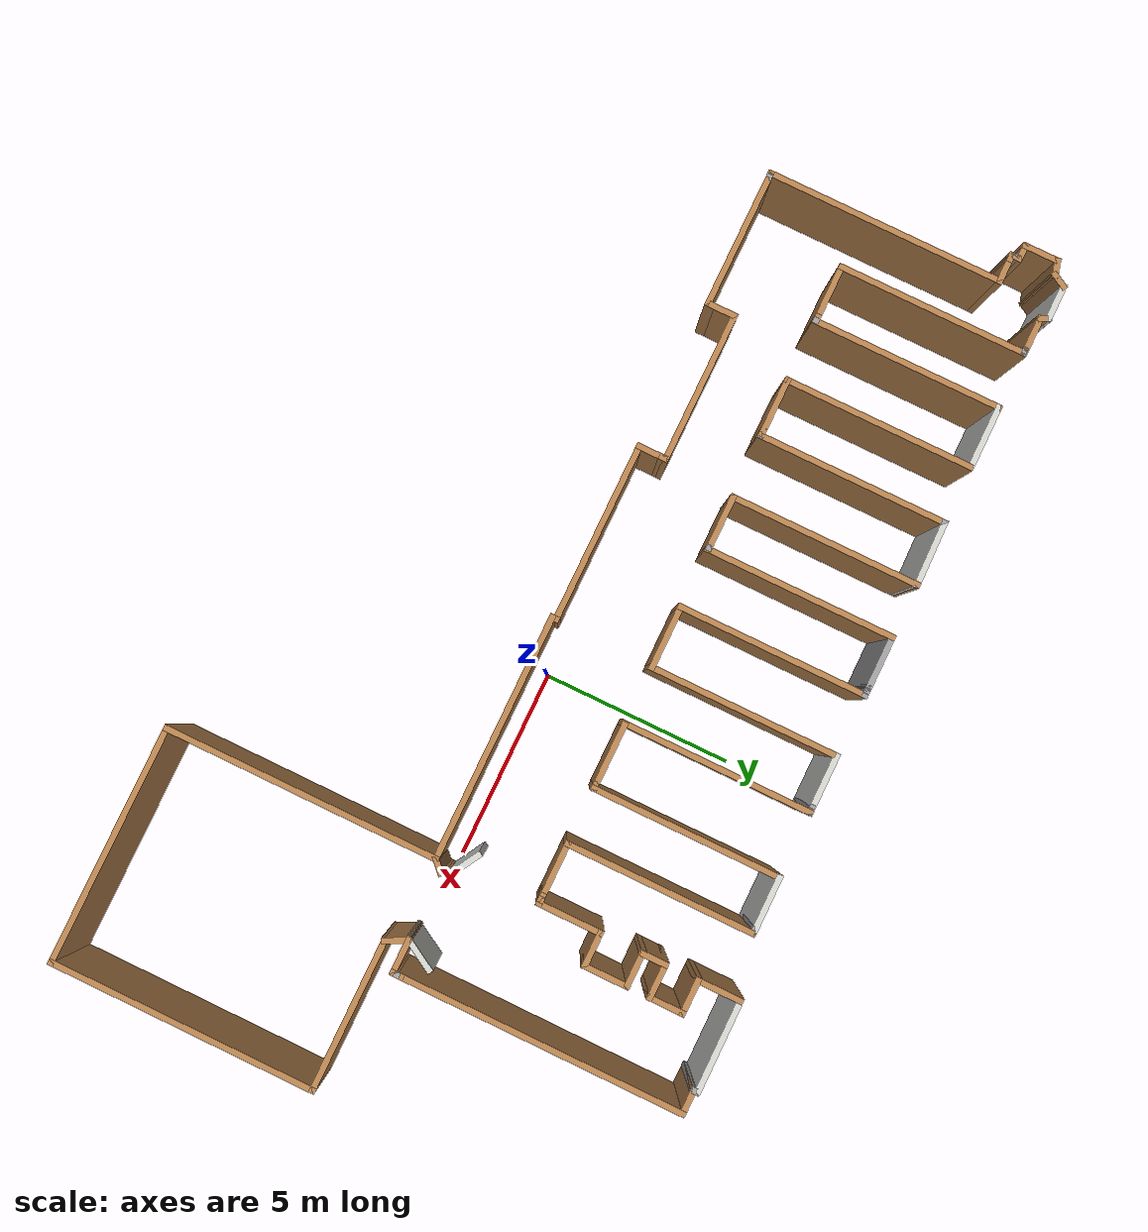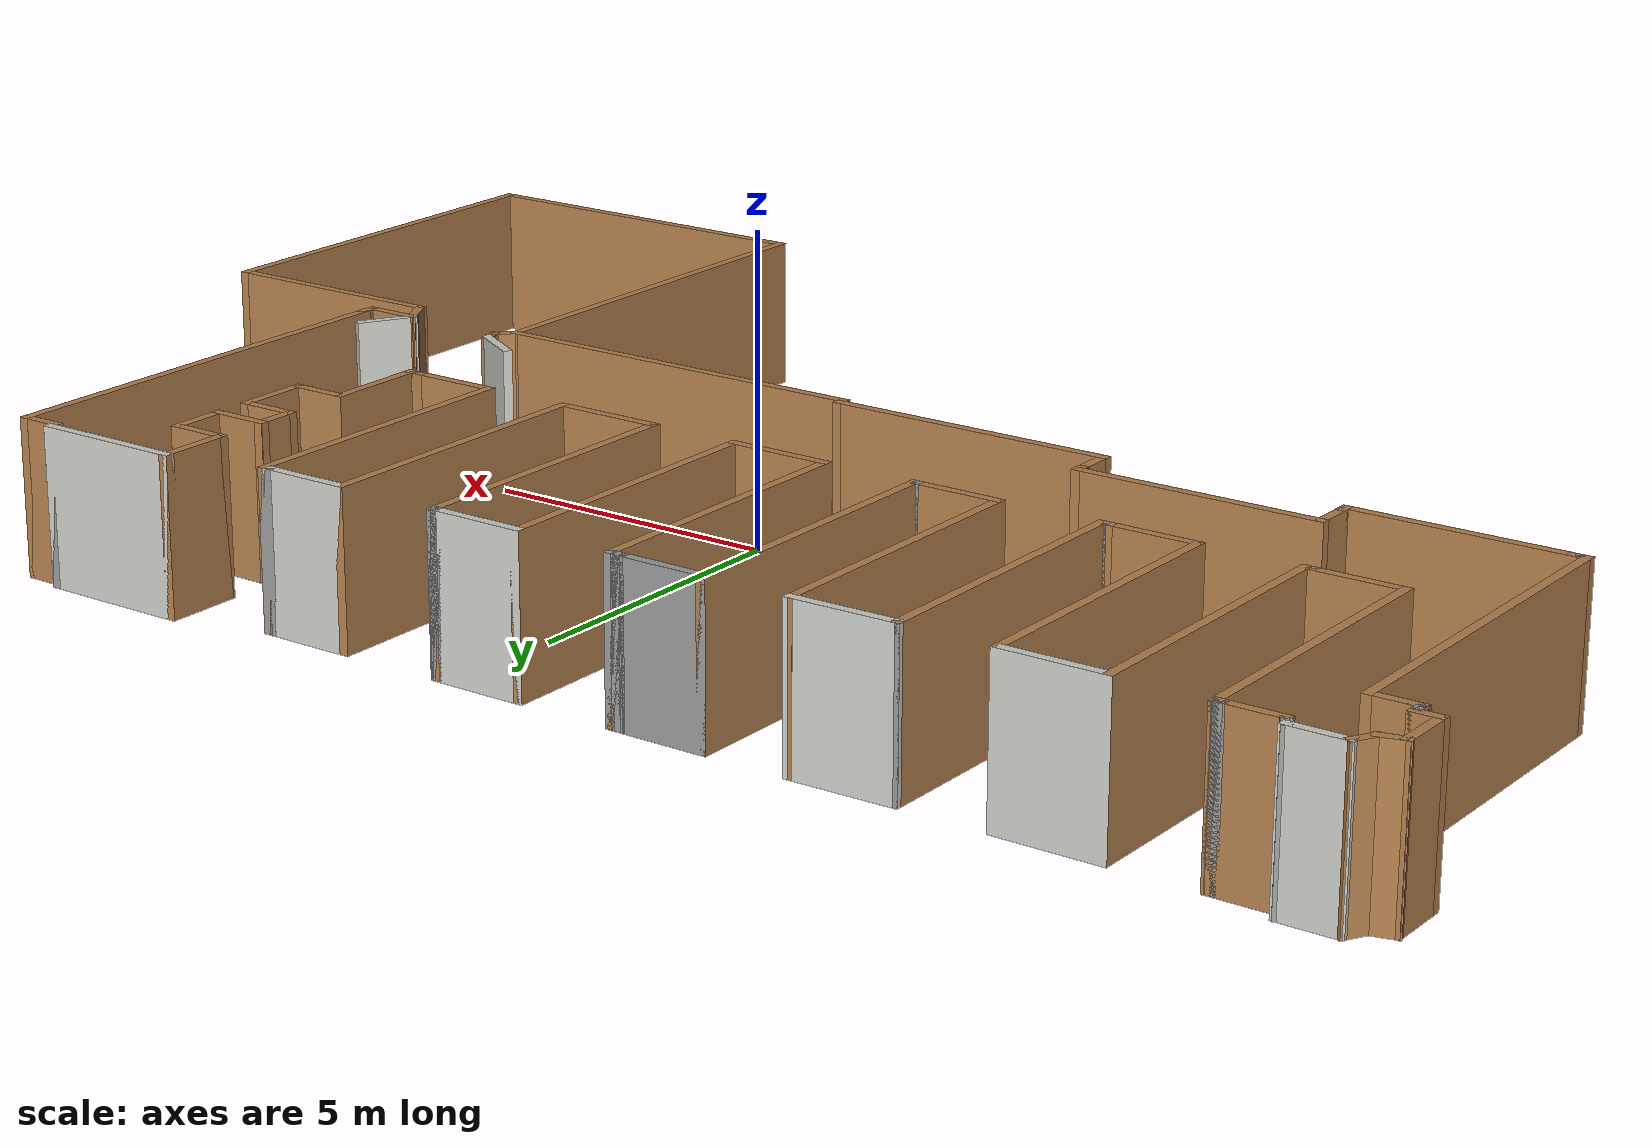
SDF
<?xml version='1.0'?>
<sdf version='1.6'>
  <model name='ecst_lab'>
    <pose frame=''>-1.55143 -0.05601 0 0 -0 0</pose>
    <link name='Wall_1'>
      <collision name='Wall_1_Collision'>
        <geometry>
          <box>
            <size>5 0.15 2.5</size>
          </box>
        </geometry>
        <pose frame=''>0 0 1.25 0 -0 0</pose>
      </collision>
      <visual name='Wall_1_Visual'>
        <pose frame=''>0 0 1.25 0 -0 0</pose>
        <geometry>
          <box>
            <size>5 0.15 2.5</size>
          </box>
        </geometry>
        <material>
          <script>
            <uri>file://media/materials/scripts/gazebo.material</uri>
            <name>Gazebo/Wood</name>
          </script>
          <ambient>1 1 1 1</ambient>
        </material>
        <meta>
          <layer>0</layer>
        </meta>
      </visual>
      <pose frame=''>-4.16301 4.67727 0 0 -0 -1.5708</pose>
    </link>
    <link name='Wall_10'>
      <collision name='Wall_10_Collision'>
        <geometry>
          <box>
            <size>1.5 0.15 2.5</size>
          </box>
        </geometry>
        <pose frame=''>0 0 1.25 0 -0 0</pose>
      </collision>
      <visual name='Wall_10_Visual'>
        <pose frame=''>0 0 1.25 0 -0 0</pose>
        <geometry>
          <box>
            <size>1.5 0.15 2.5</size>
          </box>
        </geometry>
        <material>
          <script>
            <uri>file://media/materials/scripts/gazebo.material</uri>
            <name>Gazebo/Grey</name>
          </script>
          <ambient>1 1 1 1</ambient>
        </material>
        <meta>
          <layer>0</layer>
        </meta>
      </visual>
      <pose frame=''>-2.09801 7.10227 0 0 -0 0</pose>
    </link>
    <link name='Wall_100'>
      <collision name='Wall_100_Collision'>
        <geometry>
          <box>
            <size>1 0.15 2.5</size>
          </box>
        </geometry>
        <pose frame=''>0 0 1.25 0 -0 0</pose>
      </collision>
      <visual name='Wall_100_Visual'>
        <pose frame=''>0 0 1.25 0 -0 0</pose>
        <geometry>
          <box>
            <size>1 0.15 2.5</size>
          </box>
        </geometry>
        <material>
          <script>
            <uri>file://media/materials/scripts/gazebo.material</uri>
            <name>Gazebo/Wood</name>
          </script>
          <ambient>1 1 1 1</ambient>
        </material>
        <meta>
          <layer>0</layer>
        </meta>
      </visual>
      <pose frame=''>-10.8485 7.06822 0 0 -0 0</pose>
    </link>
    <link name='Wall_101'>
      <collision name='Wall_101_Collision'>
        <geometry>
          <box>
            <size>0.15 0.15 2.5</size>
          </box>
        </geometry>
        <pose frame=''>0 0 1.25 0 -0 0</pose>
      </collision>
      <visual name='Wall_101_Visual'>
        <pose frame=''>0 0 1.25 0 -0 0</pose>
        <geometry>
          <box>
            <size>0.15 0.15 2.5</size>
          </box>
        </geometry>
        <material>
          <script>
            <uri>file://media/materials/scripts/gazebo.material</uri>
            <name>Gazebo/Grey</name>
          </script>
          <ambient>1 1 1 1</ambient>
        </material>
        <meta>
          <layer>0</layer>
        </meta>
      </visual>
      <pose frame=''>-10.4235 7.06822 0 0 -0 0</pose>
    </link>
    <link name='Wall_102'>
      <collision name='Wall_102_Collision'>
        <geometry>
          <box>
            <size>0.16 0.15 2.5</size>
          </box>
        </geometry>
        <pose frame=''>0 0 1.25 0 -0 0</pose>
      </collision>
      <visual name='Wall_102_Visual'>
        <pose frame=''>0 0 1.25 0 -0 0</pose>
        <geometry>
          <box>
            <size>0.16 0.15 2.5</size>
          </box>
        </geometry>
        <material>
          <script>
            <uri>file://media/materials/scripts/gazebo.material</uri>
            <name>Gazebo/Grey</name>
          </script>
          <ambient>1 1 1 1</ambient>
        </material>
        <meta>
          <layer>0</layer>
        </meta>
      </visual>
      <pose frame=''>-10.4185 7.06822 0 0 -0 0</pose>
    </link>
    <link name='Wall_103'>
      <collision name='Wall_103_Collision'>
        <geometry>
          <box>
            <size>0.16 0.15 2.5</size>
          </box>
        </geometry>
        <pose frame=''>0 0 1.25 0 -0 0</pose>
      </collision>
      <visual name='Wall_103_Visual'>
        <pose frame=''>0 0 1.25 0 -0 0</pose>
        <geometry>
          <box>
            <size>0.16 0.15 2.5</size>
          </box>
        </geometry>
        <material>
          <script>
            <uri>file://media/materials/scripts/gazebo.material</uri>
            <name>Gazebo/Grey</name>
          </script>
          <ambient>1 1 1 1</ambient>
        </material>
        <meta>
          <layer>0</layer>
        </meta>
      </visual>
      <pose frame=''>-10.4085 7.06822 0 0 -0 0</pose>
    </link>
    <link name='Wall_104'>
      <collision name='Wall_104_Collision'>
        <geometry>
          <box>
            <size>0.16 0.15 2.5</size>
          </box>
        </geometry>
        <pose frame=''>0 0 1.25 0 -0 0</pose>
      </collision>
      <visual name='Wall_104_Visual'>
        <pose frame=''>0 0 1.25 0 -0 0</pose>
        <geometry>
          <box>
            <size>0.16 0.15 2.5</size>
          </box>
        </geometry>
        <material>
          <script>
            <uri>file://media/materials/scripts/gazebo.material</uri>
            <name>Gazebo/Wood</name>
          </script>
          <ambient>1 1 1 1</ambient>
        </material>
        <meta>
          <layer>0</layer>
        </meta>
      </visual>
      <pose frame=''>-10.3985 7.06822 0 0 -0 0</pose>
    </link>
    <link name='Wall_105'>
      <collision name='Wall_105_Collision'>
        <geometry>
          <box>
            <size>0.16 0.15 2.5</size>
          </box>
        </geometry>
        <pose frame=''>0 0 1.25 0 -0 0</pose>
      </collision>
      <visual name='Wall_105_Visual'>
        <pose frame=''>0 0 1.25 0 -0 0</pose>
        <geometry>
          <box>
            <size>0.16 0.15 2.5</size>
          </box>
        </geometry>
        <material>
          <script>
            <uri>file://media/materials/scripts/gazebo.material</uri>
            <name>Gazebo/Grey</name>
          </script>
          <ambient>1 1 1 1</ambient>
        </material>
        <meta>
          <layer>0</layer>
        </meta>
      </visual>
      <pose frame=''>-10.3885 7.06822 0 0 -0 0</pose>
    </link>
    <link name='Wall_106'>
      <collision name='Wall_106_Collision'>
        <geometry>
          <box>
            <size>0.16 0.15 2.5</size>
          </box>
        </geometry>
        <pose frame=''>0 0 1.25 0 -0 0</pose>
      </collision>
      <visual name='Wall_106_Visual'>
        <pose frame=''>0 0 1.25 0 -0 0</pose>
        <geometry>
          <box>
            <size>0.16 0.15 2.5</size>
          </box>
        </geometry>
        <material>
          <script>
            <uri>file://media/materials/scripts/gazebo.material</uri>
            <name>Gazebo/Wood</name>
          </script>
          <ambient>1 1 1 1</ambient>
        </material>
        <meta>
          <layer>0</layer>
        </meta>
      </visual>
      <pose frame=''>-10.3785 7.06822 0 0 -0 0</pose>
    </link>
    <link name='Wall_107'>
      <collision name='Wall_107_Collision'>
        <geometry>
          <box>
            <size>0.16 0.15 2.5</size>
          </box>
        </geometry>
        <pose frame=''>0 0 1.25 0 -0 0</pose>
      </collision>
      <visual name='Wall_107_Visual'>
        <pose frame=''>0 0 1.25 0 -0 0</pose>
        <geometry>
          <box>
            <size>0.16 0.15 2.5</size>
          </box>
        </geometry>
        <material>
          <script>
            <uri>file://media/materials/scripts/gazebo.material</uri>
            <name>Gazebo/Grey</name>
          </script>
          <ambient>1 1 1 1</ambient>
        </material>
        <meta>
          <layer>0</layer>
        </meta>
      </visual>
      <pose frame=''>-10.3685 7.06822 0 0 -0 0</pose>
    </link>
    <link name='Wall_108'>
      <collision name='Wall_108_Collision'>
        <geometry>
          <box>
            <size>0.16 0.15 2.5</size>
          </box>
        </geometry>
        <pose frame=''>0 0 1.25 0 -0 0</pose>
      </collision>
      <visual name='Wall_108_Visual'>
        <pose frame=''>0 0 1.25 0 -0 0</pose>
        <geometry>
          <box>
            <size>0.16 0.15 2.5</size>
          </box>
        </geometry>
        <material>
          <script>
            <uri>file://media/materials/scripts/gazebo.material</uri>
            <name>Gazebo/Grey</name>
          </script>
          <ambient>1 1 1 1</ambient>
        </material>
        <meta>
          <layer>0</layer>
        </meta>
      </visual>
      <pose frame=''>-10.3685 7.06822 0 0 -0 3.14159</pose>
    </link>
    <link name='Wall_109'>
      <collision name='Wall_109_Collision'>
        <geometry>
          <box>
            <size>0.16 0.15 2.5</size>
          </box>
        </geometry>
        <pose frame=''>0 0 1.25 0 -0 0</pose>
      </collision>
      <visual name='Wall_109_Visual'>
        <pose frame=''>0 0 1.25 0 -0 0</pose>
        <geometry>
          <box>
            <size>0.16 0.15 2.5</size>
          </box>
        </geometry>
        <material>
          <script>
            <uri>file://media/materials/scripts/gazebo.material</uri>
            <name>Gazebo/Grey</name>
          </script>
          <ambient>1 1 1 1</ambient>
        </material>
        <meta>
          <layer>0</layer>
        </meta>
      </visual>
      <pose frame=''>-10.3685 7.06822 0 0 -0 0</pose>
    </link>
    <link name='Wall_11'>
      <collision name='Wall_11_Collision'>
        <geometry>
          <box>
            <size>0.15 0.15 2.5</size>
          </box>
        </geometry>
        <pose frame=''>0 0 1.25 0 -0 0</pose>
      </collision>
      <visual name='Wall_11_Visual'>
        <pose frame=''>0 0 1.25 0 -0 0</pose>
        <geometry>
          <box>
            <size>0.15 0.15 2.5</size>
          </box>
        </geometry>
        <material>
          <script>
            <uri>file://media/materials/scripts/gazebo.material</uri>
            <name>Gazebo/Grey</name>
          </script>
          <ambient>1 1 1 1</ambient>
        </material>
        <meta>
          <layer>0</layer>
        </meta>
      </visual>
      <pose frame=''>-1.42301 7.10227 0 0 -0 0</pose>
    </link>
    <link name='Wall_110'>
      <collision name='Wall_110_Collision'>
        <geometry>
          <box>
            <size>0.16 0.15 2.5</size>
          </box>
        </geometry>
        <pose frame=''>0 0 1.25 0 -0 0</pose>
      </collision>
      <visual name='Wall_110_Visual'>
        <pose frame=''>0 0 1.25 0 -0 0</pose>
        <geometry>
          <box>
            <size>0.16 0.15 2.5</size>
          </box>
        </geometry>
        <material>
          <script>
            <uri>file://media/materials/scripts/gazebo.material</uri>
            <name>Gazebo/Grey</name>
          </script>
          <ambient>1 1 1 1</ambient>
        </material>
        <meta>
          <layer>0</layer>
        </meta>
      </visual>
      <pose frame=''>-10.3685 7.06822 0 0 -0 3.14159</pose>
    </link>
    <link name='Wall_111'>
      <collision name='Wall_111_Collision'>
        <geometry>
          <box>
            <size>0.16 0.15 2.5</size>
          </box>
        </geometry>
        <pose frame=''>0 0 1.25 0 -0 0</pose>
      </collision>
      <visual name='Wall_111_Visual'>
        <pose frame=''>0 0 1.25 0 -0 0</pose>
        <geometry>
          <box>
            <size>0.16 0.15 2.5</size>
          </box>
        </geometry>
        <material>
          <script>
            <uri>file://media/materials/scripts/gazebo.material</uri>
            <name>Gazebo/Grey</name>
          </script>
          <ambient>1 1 1 1</ambient>
        </material>
        <meta>
          <layer>0</layer>
        </meta>
      </visual>
      <pose frame=''>-10.3685 7.06822 0 0 -0 0</pose>
    </link>
    <link name='Wall_112'>
      <collision name='Wall_112_Collision'>
        <geometry>
          <box>
            <size>0.16 0.15 2.5</size>
          </box>
        </geometry>
        <pose frame=''>0 0 1.25 0 -0 0</pose>
      </collision>
      <visual name='Wall_112_Visual'>
        <pose frame=''>0 0 1.25 0 -0 0</pose>
        <geometry>
          <box>
            <size>0.16 0.15 2.5</size>
          </box>
        </geometry>
        <material>
          <script>
            <uri>file://media/materials/scripts/gazebo.material</uri>
            <name>Gazebo/Grey</name>
          </script>
          <ambient>1 1 1 1</ambient>
        </material>
        <meta>
          <layer>0</layer>
        </meta>
      </visual>
      <pose frame=''>-10.3685 7.06822 0 0 -0 3.14159</pose>
    </link>
    <link name='Wall_113'>
      <collision name='Wall_113_Collision'>
        <geometry>
          <box>
            <size>0.16 0.15 2.5</size>
          </box>
        </geometry>
        <pose frame=''>0 0 1.25 0 -0 0</pose>
      </collision>
      <visual name='Wall_113_Visual'>
        <pose frame=''>0 0 1.25 0 -0 0</pose>
        <geometry>
          <box>
            <size>0.16 0.15 2.5</size>
          </box>
        </geometry>
        <material>
          <script>
            <uri>file://media/materials/scripts/gazebo.material</uri>
            <name>Gazebo/Grey</name>
          </script>
          <ambient>1 1 1 1</ambient>
        </material>
        <meta>
          <layer>0</layer>
        </meta>
      </visual>
      <pose frame=''>-10.3685 7.06822 0 0 -0 0</pose>
    </link>
    <link name='Wall_114'>
      <collision name='Wall_114_Collision'>
        <geometry>
          <box>
            <size>0.16 0.15 2.5</size>
          </box>
        </geometry>
        <pose frame=''>0 0 1.25 0 -0 0</pose>
      </collision>
      <visual name='Wall_114_Visual'>
        <pose frame=''>0 0 1.25 0 -0 0</pose>
        <geometry>
          <box>
            <size>0.16 0.15 2.5</size>
          </box>
        </geometry>
        <material>
          <script>
            <uri>file://media/materials/scripts/gazebo.material</uri>
            <name>Gazebo/Grey</name>
          </script>
          <ambient>1 1 1 1</ambient>
        </material>
        <meta>
          <layer>0</layer>
        </meta>
      </visual>
      <pose frame=''>-10.3685 7.06822 0 0 -0 3.14159</pose>
    </link>
    <link name='Wall_115'>
      <collision name='Wall_115_Collision'>
        <geometry>
          <box>
            <size>0.16 0.15 2.5</size>
          </box>
        </geometry>
        <pose frame=''>0 0 1.25 0 -0 0</pose>
      </collision>
      <visual name='Wall_115_Visual'>
        <pose frame=''>0 0 1.25 0 -0 0</pose>
        <geometry>
          <box>
            <size>0.16 0.15 2.5</size>
          </box>
        </geometry>
        <material>
          <script>
            <uri>file://media/materials/scripts/gazebo.material</uri>
            <name>Gazebo/Wood</name>
          </script>
          <ambient>1 1 1 1</ambient>
        </material>
        <meta>
          <layer>0</layer>
        </meta>
      </visual>
      <pose frame=''>-10.3685 7.06822 0 0 -0 0</pose>
    </link>
    <link name='Wall_116'>
      <collision name='Wall_116_Collision'>
        <geometry>
          <box>
            <size>0.16 0.15 2.5</size>
          </box>
        </geometry>
        <pose frame=''>0 0 1.25 0 -0 0</pose>
      </collision>
      <visual name='Wall_116_Visual'>
        <pose frame=''>0 0 1.25 0 -0 0</pose>
        <geometry>
          <box>
            <size>0.16 0.15 2.5</size>
          </box>
        </geometry>
        <material>
          <script>
            <uri>file://media/materials/scripts/gazebo.material</uri>
            <name>Gazebo/Grey</name>
          </script>
          <ambient>1 1 1 1</ambient>
        </material>
        <meta>
          <layer>0</layer>
        </meta>
      </visual>
      <pose frame=''>-10.3585 7.06822 0 0 -0 0</pose>
    </link>
    <link name='Wall_117'>
      <collision name='Wall_117_Collision'>
        <geometry>
          <box>
            <size>0.16 0.15 2.5</size>
          </box>
        </geometry>
        <pose frame=''>0 0 1.25 0 -0 0</pose>
      </collision>
      <visual name='Wall_117_Visual'>
        <pose frame=''>0 0 1.25 0 -0 0</pose>
        <geometry>
          <box>
            <size>0.16 0.15 2.5</size>
          </box>
        </geometry>
        <material>
          <script>
            <uri>file://media/materials/scripts/gazebo.material</uri>
            <name>Gazebo/Wood</name>
          </script>
          <ambient>1 1 1 1</ambient>
        </material>
        <meta>
          <layer>0</layer>
        </meta>
      </visual>
      <pose frame=''>-10.3485 7.06822 0 0 -0 0</pose>
    </link>
    <link name='Wall_118'>
      <collision name='Wall_118_Collision'>
        <geometry>
          <box>
            <size>5 0.15 2.5</size>
          </box>
        </geometry>
        <pose frame=''>0 0 1.25 0 -0 0</pose>
      </collision>
      <visual name='Wall_118_Visual'>
        <pose frame=''>0 0 1.25 0 -0 0</pose>
        <geometry>
          <box>
            <size>5 0.15 2.5</size>
          </box>
        </geometry>
        <material>
          <script>
            <uri>file://media/materials/scripts/gazebo.material</uri>
            <name>Gazebo/Wood</name>
          </script>
          <ambient>1 1 1 1</ambient>
        </material>
        <meta>
          <layer>0</layer>
        </meta>
      </visual>
      <pose frame=''>-10.3435 4.64322 0 0 -0 -1.5708</pose>
    </link>
    <link name='Wall_119'>
      <collision name='Wall_119_Collision'>
        <geometry>
          <box>
            <size>1.5 0.15 2.5</size>
          </box>
        </geometry>
        <pose frame=''>0 0 1.25 0 -0 0</pose>
      </collision>
      <visual name='Wall_119_Visual'>
        <pose frame=''>0 0 1.25 0 -0 0</pose>
        <geometry>
          <box>
            <size>1.5 0.15 2.5</size>
          </box>
        </geometry>
        <material>
          <script>
            <uri>file://media/materials/scripts/gazebo.material</uri>
            <name>Gazebo/Wood</name>
          </script>
          <ambient>1 1 1 1</ambient>
        </material>
        <meta>
          <layer>0</layer>
        </meta>
      </visual>
      <pose frame=''>-9.6685 2.21822 0 0 -0 0</pose>
    </link>
    <link name='Wall_12'>
      <collision name='Wall_12_Collision'>
        <geometry>
          <box>
            <size>0.16 0.15 2.5</size>
          </box>
        </geometry>
        <pose frame=''>0 0 1.25 0 -0 0</pose>
      </collision>
      <visual name='Wall_12_Visual'>
        <pose frame=''>0 0 1.25 0 -0 0</pose>
        <geometry>
          <box>
            <size>0.16 0.15 2.5</size>
          </box>
        </geometry>
        <material>
          <script>
            <uri>file://media/materials/scripts/gazebo.material</uri>
            <name>Gazebo/Grey</name>
          </script>
          <ambient>1 1 1 1</ambient>
        </material>
        <meta>
          <layer>0</layer>
        </meta>
      </visual>
      <pose frame=''>-1.41801 7.10227 0 0 -0 0</pose>
    </link>
    <link name='Wall_120'>
      <collision name='Wall_120_Collision'>
        <geometry>
          <box>
            <size>0.25 0.15 2.5</size>
          </box>
        </geometry>
        <pose frame=''>0 0 1.25 0 -0 0</pose>
      </collision>
      <visual name='Wall_120_Visual'>
        <pose frame=''>0 0 1.25 0 -0 0</pose>
        <geometry>
          <box>
            <size>0.25 0.15 2.5</size>
          </box>
        </geometry>
        <material>
          <script>
            <uri>file://media/materials/scripts/gazebo.material</uri>
            <name>Gazebo/Wood</name>
          </script>
          <ambient>1 1 1 1</ambient>
        </material>
        <meta>
          <layer>0</layer>
        </meta>
      </visual>
      <pose frame=''>-8.9435 2.21822 0 0 -0 0</pose>
    </link>
    <link name='Wall_121'>
      <collision name='Wall_121_Collision'>
        <geometry>
          <box>
            <size>0.15 0.15 2.5</size>
          </box>
        </geometry>
        <pose frame=''>0 0 1.25 0 -0 0</pose>
      </collision>
      <visual name='Wall_121_Visual'>
        <pose frame=''>0 0 1.25 0 -0 0</pose>
        <geometry>
          <box>
            <size>0.15 0.15 2.5</size>
          </box>
        </geometry>
        <material>
          <script>
            <uri>file://media/materials/scripts/gazebo.material</uri>
            <name>Gazebo/Grey</name>
          </script>
          <ambient>1 1 1 1</ambient>
        </material>
        <meta>
          <layer>0</layer>
        </meta>
      </visual>
      <pose frame=''>-8.8935 2.21822 0 0 -0 0</pose>
    </link>
    <link name='Wall_122'>
      <collision name='Wall_122_Collision'>
        <geometry>
          <box>
            <size>0.16 0.15 2.5</size>
          </box>
        </geometry>
        <pose frame=''>0 0 1.25 0 -0 0</pose>
      </collision>
      <visual name='Wall_122_Visual'>
        <pose frame=''>0 0 1.25 0 -0 0</pose>
        <geometry>
          <box>
            <size>0.16 0.15 2.5</size>
          </box>
        </geometry>
        <material>
          <script>
            <uri>file://media/materials/scripts/gazebo.material</uri>
            <name>Gazebo/Wood</name>
          </script>
          <ambient>1 1 1 1</ambient>
        </material>
        <meta>
          <layer>0</layer>
        </meta>
      </visual>
      <pose frame=''>-8.8885 2.21822 0 0 -0 0</pose>
    </link>
    <link name='Wall_123'>
      <collision name='Wall_123_Collision'>
        <geometry>
          <box>
            <size>5 0.15 2.5</size>
          </box>
        </geometry>
        <pose frame=''>0 0 1.25 0 -0 0</pose>
      </collision>
      <visual name='Wall_123_Visual'>
        <pose frame=''>0 0 1.25 0 -0 0</pose>
        <geometry>
          <box>
            <size>5 0.15 2.5</size>
          </box>
        </geometry>
        <material>
          <script>
            <uri>file://media/materials/scripts/gazebo.material</uri>
            <name>Gazebo/Wood</name>
          </script>
          <ambient>1 1 1 1</ambient>
        </material>
        <meta>
          <layer>0</layer>
        </meta>
      </visual>
      <pose frame=''>-8.8835 4.64322 0 0 -0 1.5708</pose>
    </link>
    <link name='Wall_124'>
      <collision name='Wall_124_Collision'>
        <geometry>
          <box>
            <size>1.75 0.15 2.5</size>
          </box>
        </geometry>
        <pose frame=''>0 0 1.25 0 -0 0</pose>
      </collision>
      <visual name='Wall_124_Visual'>
        <pose frame=''>0 0 1.25 0 -0 0</pose>
        <geometry>
          <box>
            <size>1.75 0.15 2.5</size>
          </box>
        </geometry>
        <material>
          <script>
            <uri>file://media/materials/scripts/gazebo.material</uri>
            <name>Gazebo/CeilingTiled</name>
          </script>
          <ambient>1 1 1 1</ambient>
        </material>
        <meta>
          <layer>0</layer>
        </meta>
      </visual>
      <pose frame=''>-8.0835 7.06822 0 0 -0 0</pose>
    </link>
    <link name='Wall_125'>
      <collision name='Wall_125_Collision'>
        <geometry>
          <box>
            <size>5 0.15 2.5</size>
          </box>
        </geometry>
        <pose frame=''>0 0 1.25 0 -0 0</pose>
      </collision>
      <visual name='Wall_125_Visual'>
        <pose frame=''>0 0 1.25 0 -0 0</pose>
        <geometry>
          <box>
            <size>5 0.15 2.5</size>
          </box>
        </geometry>
        <material>
          <script>
            <uri>file://media/materials/scripts/gazebo.material</uri>
            <name>Gazebo/Wood</name>
          </script>
          <ambient>1 1 1 1</ambient>
        </material>
        <meta>
          <layer>0</layer>
        </meta>
      </visual>
      <pose frame=''>-7.2835 4.64322 0 0 -0 -1.5708</pose>
    </link>
    <link name='Wall_126'>
      <collision name='Wall_126_Collision'>
        <geometry>
          <box>
            <size>1.5 0.15 2.5</size>
          </box>
        </geometry>
        <pose frame=''>0 0 1.25 0 -0 0</pose>
      </collision>
      <visual name='Wall_126_Visual'>
        <pose frame=''>0 0 1.25 0 -0 0</pose>
        <geometry>
          <box>
            <size>1.5 0.15 2.5</size>
          </box>
        </geometry>
        <material>
          <script>
            <uri>file://media/materials/scripts/gazebo.material</uri>
            <name>Gazebo/Wood</name>
          </script>
          <ambient>1 1 1 1</ambient>
        </material>
        <meta>
          <layer>0</layer>
        </meta>
      </visual>
      <pose frame=''>-6.6085 2.21822 0 0 -0 0</pose>
    </link>
    <link name='Wall_127'>
      <collision name='Wall_127_Collision'>
        <geometry>
          <box>
            <size>0.25 0.15 2.5</size>
          </box>
        </geometry>
        <pose frame=''>0 0 1.25 0 -0 0</pose>
      </collision>
      <visual name='Wall_127_Visual'>
        <pose frame=''>0 0 1.25 0 -0 0</pose>
        <geometry>
          <box>
            <size>0.25 0.15 2.5</size>
          </box>
        </geometry>
        <material>
          <script>
            <uri>file://media/materials/scripts/gazebo.material</uri>
            <name>Gazebo/Wood</name>
          </script>
          <ambient>1 1 1 1</ambient>
        </material>
        <meta>
          <layer>0</layer>
        </meta>
      </visual>
      <pose frame=''>-5.8835 2.21822 0 0 -0 0</pose>
    </link>
    <link name='Wall_128'>
      <collision name='Wall_128_Collision'>
        <geometry>
          <box>
            <size>0.15 0.15 2.5</size>
          </box>
        </geometry>
        <pose frame=''>0 0 1.25 0 -0 0</pose>
      </collision>
      <visual name='Wall_128_Visual'>
        <pose frame=''>0 0 1.25 0 -0 0</pose>
        <geometry>
          <box>
            <size>0.15 0.15 2.5</size>
          </box>
        </geometry>
        <material>
          <script>
            <uri>file://media/materials/scripts/gazebo.material</uri>
            <name>Gazebo/Grey</name>
          </script>
          <ambient>1 1 1 1</ambient>
        </material>
        <meta>
          <layer>0</layer>
        </meta>
      </visual>
      <pose frame=''>-5.8335 2.21822 0 0 -0 0</pose>
    </link>
    <link name='Wall_129'>
      <collision name='Wall_129_Collision'>
        <geometry>
          <box>
            <size>0.16 0.15 2.5</size>
          </box>
        </geometry>
        <pose frame=''>0 0 1.25 0 -0 0</pose>
      </collision>
      <visual name='Wall_129_Visual'>
        <pose frame=''>0 0 1.25 0 -0 0</pose>
        <geometry>
          <box>
            <size>0.16 0.15 2.5</size>
          </box>
        </geometry>
        <material>
          <script>
            <uri>file://media/materials/scripts/gazebo.material</uri>
            <name>Gazebo/Wood</name>
          </script>
          <ambient>1 1 1 1</ambient>
        </material>
        <meta>
          <layer>0</layer>
        </meta>
      </visual>
      <pose frame=''>-5.8285 2.21822 0 0 -0 0</pose>
    </link>
    <link name='Wall_13'>
      <collision name='Wall_13_Collision'>
        <geometry>
          <box>
            <size>0.16 0.15 2.5</size>
          </box>
        </geometry>
        <pose frame=''>0 0 1.25 0 -0 0</pose>
      </collision>
      <visual name='Wall_13_Visual'>
        <pose frame=''>0 0 1.25 0 -0 0</pose>
        <geometry>
          <box>
            <size>0.16 0.15 2.5</size>
          </box>
        </geometry>
        <material>
          <script>
            <uri>file://media/materials/scripts/gazebo.material</uri>
            <name>Gazebo/Grey</name>
          </script>
          <ambient>1 1 1 1</ambient>
        </material>
        <meta>
          <layer>0</layer>
        </meta>
      </visual>
      <pose frame=''>-1.40801 7.10227 0 0 -0 0</pose>
    </link>
    <link name='Wall_130'>
      <collision name='Wall_130_Collision'>
        <geometry>
          <box>
            <size>0.16 0.15 2.5</size>
          </box>
        </geometry>
        <pose frame=''>0 0 1.25 0 -0 0</pose>
      </collision>
      <visual name='Wall_130_Visual'>
        <pose frame=''>0 0 1.25 0 -0 0</pose>
        <geometry>
          <box>
            <size>0.16 0.15 2.5</size>
          </box>
        </geometry>
        <material>
          <script>
            <uri>file://media/materials/scripts/gazebo.material</uri>
            <name>Gazebo/Grey</name>
          </script>
          <ambient>1 1 1 1</ambient>
        </material>
        <meta>
          <layer>0</layer>
        </meta>
      </visual>
      <pose frame=''>-5.8185 2.21822 0 0 -0 0</pose>
    </link>
    <link name='Wall_131'>
      <collision name='Wall_131_Collision'>
        <geometry>
          <box>
            <size>0.16 0.15 2.5</size>
          </box>
        </geometry>
        <pose frame=''>0 0 1.25 0 -0 0</pose>
      </collision>
      <visual name='Wall_131_Visual'>
        <pose frame=''>0 0 1.25 0 -0 0</pose>
        <geometry>
          <box>
            <size>0.16 0.15 2.5</size>
          </box>
        </geometry>
        <material>
          <script>
            <uri>file://media/materials/scripts/gazebo.material</uri>
            <name>Gazebo/Grey</name>
          </script>
          <ambient>1 1 1 1</ambient>
        </material>
        <meta>
          <layer>0</layer>
        </meta>
      </visual>
      <pose frame=''>-5.8085 2.21822 0 0 -0 0</pose>
    </link>
    <link name='Wall_132'>
      <collision name='Wall_132_Collision'>
        <geometry>
          <box>
            <size>0.16 0.15 2.5</size>
          </box>
        </geometry>
        <pose frame=''>0 0 1.25 0 -0 0</pose>
      </collision>
      <visual name='Wall_132_Visual'>
        <pose frame=''>0 0 1.25 0 -0 0</pose>
        <geometry>
          <box>
            <size>0.16 0.15 2.5</size>
          </box>
        </geometry>
        <material>
          <script>
            <uri>file://media/materials/scripts/gazebo.material</uri>
            <name>Gazebo/Wood</name>
          </script>
          <ambient>1 1 1 1</ambient>
        </material>
        <meta>
          <layer>0</layer>
        </meta>
      </visual>
      <pose frame=''>-5.7985 2.21822 0 0 -0 0</pose>
    </link>
    <link name='Wall_133'>
      <collision name='Wall_133_Collision'>
        <geometry>
          <box>
            <size>5 0.15 2.5</size>
          </box>
        </geometry>
        <pose frame=''>0 0 1.25 0 -0 0</pose>
      </collision>
      <visual name='Wall_133_Visual'>
        <pose frame=''>0 0 1.25 0 -0 0</pose>
        <geometry>
          <box>
            <size>5 0.15 2.5</size>
          </box>
        </geometry>
        <material>
          <script>
            <uri>file://media/materials/scripts/gazebo.material</uri>
            <name>Gazebo/Wood</name>
          </script>
          <ambient>1 1 1 1</ambient>
        </material>
        <meta>
          <layer>0</layer>
        </meta>
      </visual>
      <pose frame=''>-5.7935 4.64322 0 0 -0 1.5708</pose>
    </link>
    <link name='Wall_134'>
      <collision name='Wall_134_Collision'>
        <geometry>
          <box>
            <size>0.15 0.15 2.5</size>
          </box>
        </geometry>
        <pose frame=''>0 0 1.25 0 -0 0</pose>
      </collision>
      <visual name='Wall_134_Visual'>
        <pose frame=''>0 0 1.25 0 -0 0</pose>
        <geometry>
          <box>
            <size>0.15 0.15 2.5</size>
          </box>
        </geometry>
        <material>
          <script>
            <uri>file://media/materials/scripts/gazebo.material</uri>
            <name>Gazebo/Grey</name>
          </script>
          <ambient>1 1 1 1</ambient>
        </material>
        <meta>
          <layer>0</layer>
        </meta>
      </visual>
      <pose frame=''>-5.7935 7.06822 0 0 -0 0</pose>
    </link>
    <link name='Wall_135'>
      <collision name='Wall_135_Collision'>
        <geometry>
          <box>
            <size>0.15 0.15 2.5</size>
          </box>
        </geometry>
        <pose frame=''>0 0 1.25 0 -0 0</pose>
      </collision>
      <visual name='Wall_135_Visual'>
        <pose frame=''>0 0 1.25 0 -0 0</pose>
        <geometry>
          <box>
            <size>0.15 0.15 2.5</size>
          </box>
        </geometry>
        <material>
          <script>
            <uri>file://media/materials/scripts/gazebo.material</uri>
            <name>Gazebo/Grey</name>
          </script>
          <ambient>1 1 1 1</ambient>
        </material>
        <meta>
          <layer>0</layer>
        </meta>
      </visual>
      <pose frame=''>-5.7935 7.06822 0 0 -0 0</pose>
    </link>
    <link name='Wall_136'>
      <collision name='Wall_136_Collision'>
        <geometry>
          <box>
            <size>0.15 0.15 2.5</size>
          </box>
        </geometry>
        <pose frame=''>0 0 1.25 0 -0 0</pose>
      </collision>
      <visual name='Wall_136_Visual'>
        <pose frame=''>0 0 1.25 0 -0 0</pose>
        <geometry>
          <box>
            <size>0.15 0.15 2.5</size>
          </box>
        </geometry>
        <material>
          <script>
            <uri>file://media/materials/scripts/gazebo.material</uri>
            <name>Gazebo/Grey</name>
          </script>
          <ambient>1 1 1 1</ambient>
        </material>
        <meta>
          <layer>0</layer>
        </meta>
      </visual>
      <pose frame=''>-5.7935 7.06822 0 0 -0 0</pose>
    </link>
    <link name='Wall_137'>
      <collision name='Wall_137_Collision'>
        <geometry>
          <box>
            <size>0.15 0.15 2.5</size>
          </box>
        </geometry>
        <pose frame=''>0 0 1.25 0 -0 0</pose>
      </collision>
      <visual name='Wall_137_Visual'>
        <pose frame=''>0 0 1.25 0 -0 0</pose>
        <geometry>
          <box>
            <size>0.15 0.15 2.5</size>
          </box>
        </geometry>
        <material>
          <script>
            <uri>file://media/materials/scripts/gazebo.material</uri>
            <name>Gazebo/Grey</name>
          </script>
          <ambient>1 1 1 1</ambient>
        </material>
        <meta>
          <layer>0</layer>
        </meta>
      </visual>
      <pose frame=''>-5.7935 7.06822 0 0 -0 0</pose>
    </link>
    <link name='Wall_138'>
      <collision name='Wall_138_Collision'>
        <geometry>
          <box>
            <size>1.78084 0.15 2.5</size>
          </box>
        </geometry>
        <pose frame=''>0 0 1.25 0 -0 0</pose>
      </collision>
      <visual name='Wall_138_Visual'>
        <pose frame=''>0 0 1.25 0 -0 0</pose>
        <geometry>
          <box>
            <size>1.78084 0.15 2.5</size>
          </box>
        </geometry>
        <material>
          <script>
            <uri>file://media/materials/scripts/gazebo.material</uri>
            <name>Gazebo/CeilingTiled</name>
          </script>
          <ambient>1 1 1 1</ambient>
        </material>
        <meta>
          <layer>0</layer>
        </meta>
      </visual>
      <pose frame=''>-4.97826 7.08524 0 0 -0 0.020886</pose>
    </link>
    <link name='Wall_14'>
      <collision name='Wall_14_Collision'>
        <geometry>
          <box>
            <size>0.16 0.15 2.5</size>
          </box>
        </geometry>
        <pose frame=''>0 0 1.25 0 -0 0</pose>
      </collision>
      <visual name='Wall_14_Visual'>
        <pose frame=''>0 0 1.25 0 -0 0</pose>
        <geometry>
          <box>
            <size>0.16 0.15 2.5</size>
          </box>
        </geometry>
        <material>
          <script>
            <uri>file://media/materials/scripts/gazebo.material</uri>
            <name>Gazebo/Grey</name>
          </script>
          <ambient>1 1 1 1</ambient>
        </material>
        <meta>
          <layer>0</layer>
        </meta>
      </visual>
      <pose frame=''>-1.39801 7.10227 0 0 -0 0</pose>
    </link>
    <link name='Wall_15'>
      <collision name='Wall_15_Collision'>
        <geometry>
          <box>
            <size>0.16 0.15 2.5</size>
          </box>
        </geometry>
        <pose frame=''>0 0 1.25 0 -0 0</pose>
      </collision>
      <visual name='Wall_15_Visual'>
        <pose frame=''>0 0 1.25 0 -0 0</pose>
        <geometry>
          <box>
            <size>0.16 0.15 2.5</size>
          </box>
        </geometry>
        <material>
          <script>
            <uri>file://media/materials/scripts/gazebo.material</uri>
            <name>Gazebo/Grey</name>
          </script>
          <ambient>1 1 1 1</ambient>
        </material>
        <meta>
          <layer>0</layer>
        </meta>
      </visual>
      <pose frame=''>-1.38801 7.10227 0 0 -0 0</pose>
    </link>
    <link name='Wall_16'>
      <collision name='Wall_16_Collision'>
        <geometry>
          <box>
            <size>0.16 0.15 2.5</size>
          </box>
        </geometry>
        <pose frame=''>0 0 1.25 0 -0 0</pose>
      </collision>
      <visual name='Wall_16_Visual'>
        <pose frame=''>0 0 1.25 0 -0 0</pose>
        <geometry>
          <box>
            <size>0.16 0.15 2.5</size>
          </box>
        </geometry>
        <material>
          <script>
            <uri>file://media/materials/scripts/gazebo.material</uri>
            <name>Gazebo/Grey</name>
          </script>
          <ambient>1 1 1 1</ambient>
        </material>
        <meta>
          <layer>0</layer>
        </meta>
      </visual>
      <pose frame=''>-1.37801 7.10227 0 0 -0 0</pose>
    </link>
    <link name='Wall_17'>
      <collision name='Wall_17_Collision'>
        <geometry>
          <box>
            <size>0.16 0.15 2.5</size>
          </box>
        </geometry>
        <pose frame=''>0 0 1.25 0 -0 0</pose>
      </collision>
      <visual name='Wall_17_Visual'>
        <pose frame=''>0 0 1.25 0 -0 0</pose>
        <geometry>
          <box>
            <size>0.16 0.15 2.5</size>
          </box>
        </geometry>
        <material>
          <script>
            <uri>file://media/materials/scripts/gazebo.material</uri>
            <name>Gazebo/Grey</name>
          </script>
          <ambient>1 1 1 1</ambient>
        </material>
        <meta>
          <layer>0</layer>
        </meta>
      </visual>
      <pose frame=''>-1.36801 7.10227 0 0 -0 0</pose>
    </link>
    <link name='Wall_18'>
      <collision name='Wall_18_Collision'>
        <geometry>
          <box>
            <size>0.16 0.15 2.5</size>
          </box>
        </geometry>
        <pose frame=''>0 0 1.25 0 -0 0</pose>
      </collision>
      <visual name='Wall_18_Visual'>
        <pose frame=''>0 0 1.25 0 -0 0</pose>
        <geometry>
          <box>
            <size>0.16 0.15 2.5</size>
          </box>
        </geometry>
        <material>
          <script>
            <uri>file://media/materials/scripts/gazebo.material</uri>
            <name>Gazebo/Grey</name>
          </script>
          <ambient>1 1 1 1</ambient>
        </material>
        <meta>
          <layer>0</layer>
        </meta>
      </visual>
      <pose frame=''>-1.35801 7.10227 0 0 -0 0</pose>
    </link>
    <link name='Wall_19'>
      <collision name='Wall_19_Collision'>
        <geometry>
          <box>
            <size>0.16 0.15 2.5</size>
          </box>
        </geometry>
        <pose frame=''>0 0 1.25 0 -0 0</pose>
      </collision>
      <visual name='Wall_19_Visual'>
        <pose frame=''>0 0 1.25 0 -0 0</pose>
        <geometry>
          <box>
            <size>0.16 0.15 2.5</size>
          </box>
        </geometry>
        <material>
          <script>
            <uri>file://media/materials/scripts/gazebo.material</uri>
            <name>Gazebo/Grey</name>
          </script>
          <ambient>1 1 1 1</ambient>
        </material>
        <meta>
          <layer>0</layer>
        </meta>
      </visual>
      <pose frame=''>-1.34801 7.10227 0 0 -0 0</pose>
    </link>
    <link name='Wall_2'>
      <collision name='Wall_2_Collision'>
        <geometry>
          <box>
            <size>1.5 0.15 2.5</size>
          </box>
        </geometry>
        <pose frame=''>0 0 1.25 0 -0 0</pose>
      </collision>
      <visual name='Wall_2_Visual'>
        <pose frame=''>0 0 1.25 0 -0 0</pose>
        <geometry>
          <box>
            <size>1.5 0.15 2.5</size>
          </box>
        </geometry>
        <material>
          <script>
            <uri>file://media/materials/scripts/gazebo.material</uri>
            <name>Gazebo/Wood</name>
          </script>
          <ambient>1 1 1 1</ambient>
        </material>
        <meta>
          <layer>0</layer>
        </meta>
      </visual>
      <pose frame=''>-3.48801 2.25228 0 0 -0 0</pose>
    </link>
    <link name='Wall_20'>
      <collision name='Wall_20_Collision'>
        <geometry>
          <box>
            <size>0.25 0.15 2.5</size>
          </box>
        </geometry>
        <pose frame=''>0 0 1.25 0 -0 0</pose>
      </collision>
      <visual name='Wall_20_Visual'>
        <pose frame=''>0 0 1.25 0 -0 0</pose>
        <geometry>
          <box>
            <size>0.25 0.15 2.5</size>
          </box>
        </geometry>
        <material>
          <script>
            <uri>file://media/materials/scripts/gazebo.material</uri>
            <name>Gazebo/Grey</name>
          </script>
          <ambient>1 1 1 1</ambient>
        </material>
        <meta>
          <layer>0</layer>
        </meta>
      </visual>
      <pose frame=''>-1.29301 7.10227 0 0 -0 0</pose>
    </link>
    <link name='Wall_21'>
      <collision name='Wall_21_Collision'>
        <geometry>
          <box>
            <size>5 0.15 2.5</size>
          </box>
        </geometry>
        <pose frame=''>0 0 1.25 0 -0 0</pose>
      </collision>
      <visual name='Wall_21_Visual'>
        <pose frame=''>0 0 1.25 0 -0 0</pose>
        <geometry>
          <box>
            <size>5 0.15 2.5</size>
          </box>
        </geometry>
        <material>
          <script>
            <uri>file://media/materials/scripts/gazebo.material</uri>
            <name>Gazebo/Wood</name>
          </script>
          <ambient>1 1 1 1</ambient>
        </material>
        <meta>
          <layer>0</layer>
        </meta>
      </visual>
      <pose frame=''>-1.24301 4.67727 0 0 -0 -1.5708</pose>
    </link>
    <link name='Wall_22'>
      <collision name='Wall_22_Collision'>
        <geometry>
          <box>
            <size>1.75 0.15 2.5</size>
          </box>
        </geometry>
        <pose frame=''>0 0 1.25 0 -0 0</pose>
      </collision>
      <visual name='Wall_22_Visual'>
        <pose frame=''>0 0 1.25 0 -0 0</pose>
        <geometry>
          <box>
            <size>1.75 0.15 2.5</size>
          </box>
        </geometry>
        <material>
          <script>
            <uri>file://media/materials/scripts/gazebo.material</uri>
            <name>Gazebo/Wood</name>
          </script>
          <ambient>1 1 1 1</ambient>
        </material>
        <meta>
          <layer>0</layer>
        </meta>
      </visual>
      <pose frame=''>-0.443013 2.25228 0 0 -0 0</pose>
    </link>
    <link name='Wall_23'>
      <collision name='Wall_23_Collision'>
        <geometry>
          <box>
            <size>5 0.15 2.5</size>
          </box>
        </geometry>
        <pose frame=''>0 0 1.25 0 -0 0</pose>
      </collision>
      <visual name='Wall_23_Visual'>
        <pose frame=''>0 0 1.25 0 -0 0</pose>
        <geometry>
          <box>
            <size>5 0.15 2.5</size>
          </box>
        </geometry>
        <material>
          <script>
            <uri>file://media/materials/scripts/gazebo.material</uri>
            <name>Gazebo/Wood</name>
          </script>
          <ambient>1 1 1 1</ambient>
        </material>
        <meta>
          <layer>0</layer>
        </meta>
      </visual>
      <pose frame=''>0.356987 4.67727 0 0 -0 1.5708</pose>
    </link>
    <link name='Wall_24'>
      <collision name='Wall_24_Collision'>
        <geometry>
          <box>
            <size>1.5 0.15 2.5</size>
          </box>
        </geometry>
        <pose frame=''>0 0 1.25 0 -0 0</pose>
      </collision>
      <visual name='Wall_24_Visual'>
        <pose frame=''>0 0 1.25 0 -0 0</pose>
        <geometry>
          <box>
            <size>1.5 0.15 2.5</size>
          </box>
        </geometry>
        <material>
          <script>
            <uri>file://media/materials/scripts/gazebo.material</uri>
            <name>Gazebo/CeilingTiled</name>
          </script>
          <ambient>1 1 1 1</ambient>
        </material>
        <meta>
          <layer>0</layer>
        </meta>
      </visual>
      <pose frame=''>1.03199 7.10227 0 0 -0 0</pose>
    </link>
    <link name='Wall_25'>
      <collision name='Wall_25_Collision'>
        <geometry>
          <box>
            <size>0.25 0.15 2.5</size>
          </box>
        </geometry>
        <pose frame=''>0 0 1.25 0 -0 0</pose>
      </collision>
      <visual name='Wall_25_Visual'>
        <pose frame=''>0 0 1.25 0 -0 0</pose>
        <geometry>
          <box>
            <size>0.25 0.15 2.5</size>
          </box>
        </geometry>
        <material>
          <script>
            <uri>file://media/materials/scripts/gazebo.material</uri>
            <name>Gazebo/Grey</name>
          </script>
          <ambient>1 1 1 1</ambient>
        </material>
        <meta>
          <layer>0</layer>
        </meta>
      </visual>
      <pose frame=''>1.75699 7.10227 0 0 -0 0</pose>
    </link>
    <link name='Wall_26'>
      <collision name='Wall_26_Collision'>
        <geometry>
          <box>
            <size>0.15 0.15 2.5</size>
          </box>
        </geometry>
        <pose frame=''>0 0 1.25 0 -0 0</pose>
      </collision>
      <visual name='Wall_26_Visual'>
        <pose frame=''>0 0 1.25 0 -0 0</pose>
        <geometry>
          <box>
            <size>0.15 0.15 2.5</size>
          </box>
        </geometry>
        <material>
          <script>
            <uri>file://media/materials/scripts/gazebo.material</uri>
            <name>Gazebo/Grey</name>
          </script>
          <ambient>1 1 1 1</ambient>
        </material>
        <meta>
          <layer>0</layer>
        </meta>
      </visual>
      <pose frame=''>1.80699 7.10227 0 0 -0 0</pose>
    </link>
    <link name='Wall_27'>
      <collision name='Wall_27_Collision'>
        <geometry>
          <box>
            <size>0.16 0.15 2.5</size>
          </box>
        </geometry>
        <pose frame=''>0 0 1.25 0 -0 0</pose>
      </collision>
      <visual name='Wall_27_Visual'>
        <pose frame=''>0 0 1.25 0 -0 0</pose>
        <geometry>
          <box>
            <size>0.16 0.15 2.5</size>
          </box>
        </geometry>
        <material>
          <script>
            <uri>file://media/materials/scripts/gazebo.material</uri>
            <name>Gazebo/Grey</name>
          </script>
          <ambient>1 1 1 1</ambient>
        </material>
        <meta>
          <layer>0</layer>
        </meta>
      </visual>
      <pose frame=''>1.81199 7.10227 0 0 -0 0</pose>
    </link>
    <link name='Wall_28'>
      <collision name='Wall_28_Collision'>
        <geometry>
          <box>
            <size>0.16 0.15 2.5</size>
          </box>
        </geometry>
        <pose frame=''>0 0 1.25 0 -0 0</pose>
      </collision>
      <visual name='Wall_28_Visual'>
        <pose frame=''>0 0 1.25 0 -0 0</pose>
        <geometry>
          <box>
            <size>0.16 0.15 2.5</size>
          </box>
        </geometry>
        <material>
          <script>
            <uri>file://media/materials/scripts/gazebo.material</uri>
            <name>Gazebo/Grey</name>
          </script>
          <ambient>1 1 1 1</ambient>
        </material>
        <meta>
          <layer>0</layer>
        </meta>
      </visual>
      <pose frame=''>1.82199 7.10227 0 0 -0 0</pose>
    </link>
    <link name='Wall_29'>
      <collision name='Wall_29_Collision'>
        <geometry>
          <box>
            <size>0.16 0.15 2.5</size>
          </box>
        </geometry>
        <pose frame=''>0 0 1.25 0 -0 0</pose>
      </collision>
      <visual name='Wall_29_Visual'>
        <pose frame=''>0 0 1.25 0 -0 0</pose>
        <geometry>
          <box>
            <size>0.16 0.15 2.5</size>
          </box>
        </geometry>
        <material>
          <script>
            <uri>file://media/materials/scripts/gazebo.material</uri>
            <name>Gazebo/Grey</name>
          </script>
          <ambient>1 1 1 1</ambient>
        </material>
        <meta>
          <layer>0</layer>
        </meta>
      </visual>
      <pose frame=''>1.82199 7.10227 0 0 -0 3.14159</pose>
    </link>
    <link name='Wall_3'>
      <collision name='Wall_3_Collision'>
        <geometry>
          <box>
            <size>0.15 0.15 2.5</size>
          </box>
        </geometry>
        <pose frame=''>0 0 1.25 0 -0 0</pose>
      </collision>
      <visual name='Wall_3_Visual'>
        <pose frame=''>0 0 1.25 0 -0 0</pose>
        <geometry>
          <box>
            <size>0.15 0.15 2.5</size>
          </box>
        </geometry>
        <material>
          <script>
            <uri>file://media/materials/scripts/gazebo.material</uri>
            <name>Gazebo/Grey</name>
          </script>
          <ambient>1 1 1 1</ambient>
        </material>
        <meta>
          <layer>0</layer>
        </meta>
      </visual>
      <pose frame=''>-2.81301 2.25228 0 0 -0 0</pose>
    </link>
    <link name='Wall_30'>
      <collision name='Wall_30_Collision'>
        <geometry>
          <box>
            <size>0.16 0.15 2.5</size>
          </box>
        </geometry>
        <pose frame=''>0 0 1.25 0 -0 0</pose>
      </collision>
      <visual name='Wall_30_Visual'>
        <pose frame=''>0 0 1.25 0 -0 0</pose>
        <geometry>
          <box>
            <size>0.16 0.15 2.5</size>
          </box>
        </geometry>
        <material>
          <script>
            <uri>file://media/materials/scripts/gazebo.material</uri>
            <name>Gazebo/Grey</name>
          </script>
          <ambient>1 1 1 1</ambient>
        </material>
        <meta>
          <layer>0</layer>
        </meta>
      </visual>
      <pose frame=''>1.82199 7.10227 0 0 -0 0</pose>
    </link>
    <link name='Wall_31'>
      <collision name='Wall_31_Collision'>
        <geometry>
          <box>
            <size>0.16 0.15 2.5</size>
          </box>
        </geometry>
        <pose frame=''>0 0 1.25 0 -0 0</pose>
      </collision>
      <visual name='Wall_31_Visual'>
        <pose frame=''>0 0 1.25 0 -0 0</pose>
        <geometry>
          <box>
            <size>0.16 0.15 2.5</size>
          </box>
        </geometry>
        <material>
          <script>
            <uri>file://media/materials/scripts/gazebo.material</uri>
            <name>Gazebo/Grey</name>
          </script>
          <ambient>1 1 1 1</ambient>
        </material>
        <meta>
          <layer>0</layer>
        </meta>
      </visual>
      <pose frame=''>1.83199 7.10227 0 0 -0 0</pose>
    </link>
    <link name='Wall_32'>
      <collision name='Wall_32_Collision'>
        <geometry>
          <box>
            <size>0.16 0.15 2.5</size>
          </box>
        </geometry>
        <pose frame=''>0 0 1.25 0 -0 0</pose>
      </collision>
      <visual name='Wall_32_Visual'>
        <pose frame=''>0 0 1.25 0 -0 0</pose>
        <geometry>
          <box>
            <size>0.16 0.15 2.5</size>
          </box>
        </geometry>
        <material>
          <script>
            <uri>file://media/materials/scripts/gazebo.material</uri>
            <name>Gazebo/Grey</name>
          </script>
          <ambient>1 1 1 1</ambient>
        </material>
        <meta>
          <layer>0</layer>
        </meta>
      </visual>
      <pose frame=''>1.83199 7.10227 0 0 -0 3.14159</pose>
    </link>
    <link name='Wall_33'>
      <collision name='Wall_33_Collision'>
        <geometry>
          <box>
            <size>0.16 0.15 2.5</size>
          </box>
        </geometry>
        <pose frame=''>0 0 1.25 0 -0 0</pose>
      </collision>
      <visual name='Wall_33_Visual'>
        <pose frame=''>0 0 1.25 0 -0 0</pose>
        <geometry>
          <box>
            <size>0.16 0.15 2.5</size>
          </box>
        </geometry>
        <material>
          <script>
            <uri>file://media/materials/scripts/gazebo.material</uri>
            <name>Gazebo/Grey</name>
          </script>
          <ambient>1 1 1 1</ambient>
        </material>
        <meta>
          <layer>0</layer>
        </meta>
      </visual>
      <pose frame=''>1.83199 7.10227 0 0 -0 0</pose>
    </link>
    <link name='Wall_34'>
      <collision name='Wall_34_Collision'>
        <geometry>
          <box>
            <size>5 0.15 2.5</size>
          </box>
        </geometry>
        <pose frame=''>0 0 1.25 0 -0 0</pose>
      </collision>
      <visual name='Wall_34_Visual'>
        <pose frame=''>0 0 1.25 0 -0 0</pose>
        <geometry>
          <box>
            <size>5 0.15 2.5</size>
          </box>
        </geometry>
        <material>
          <script>
            <uri>file://media/materials/scripts/gazebo.material</uri>
            <name>Gazebo/Wood</name>
          </script>
          <ambient>1 1 1 1</ambient>
        </material>
        <meta>
          <layer>0</layer>
        </meta>
      </visual>
      <pose frame=''>1.83699 4.67727 0 0 -0 -1.5708</pose>
    </link>
    <link name='Wall_35'>
      <collision name='Wall_35_Collision'>
        <geometry>
          <box>
            <size>1.75 0.15 2.5</size>
          </box>
        </geometry>
        <pose frame=''>0 0 1.25 0 -0 0</pose>
      </collision>
      <visual name='Wall_35_Visual'>
        <pose frame=''>0 0 1.25 0 -0 0</pose>
        <geometry>
          <box>
            <size>1.75 0.15 2.5</size>
          </box>
        </geometry>
        <material>
          <script>
            <uri>file://media/materials/scripts/gazebo.material</uri>
            <name>Gazebo/Wood</name>
          </script>
          <ambient>1 1 1 1</ambient>
        </material>
        <meta>
          <layer>0</layer>
        </meta>
      </visual>
      <pose frame=''>2.63699 2.25228 0 0 -0 0</pose>
    </link>
    <link name='Wall_36'>
      <collision name='Wall_36_Collision'>
        <geometry>
          <box>
            <size>0.25 0.15 2.5</size>
          </box>
        </geometry>
        <pose frame=''>0 0 1.25 0 -0 0</pose>
      </collision>
      <visual name='Wall_36_Visual'>
        <pose frame=''>0 0 1.25 0 -0 0</pose>
        <geometry>
          <box>
            <size>0.25 0.15 2.5</size>
          </box>
        </geometry>
        <material>
          <script>
            <uri>file://media/materials/scripts/gazebo.material</uri>
            <name>Gazebo/Wood</name>
          </script>
          <ambient>1 1 1 1</ambient>
        </material>
        <meta>
          <layer>0</layer>
        </meta>
      </visual>
      <pose frame=''>3.48699 2.25228 0 0 -0 0</pose>
    </link>
    <link name='Wall_37'>
      <collision name='Wall_37_Collision'>
        <geometry>
          <box>
            <size>5 0.15 2.5</size>
          </box>
        </geometry>
        <pose frame=''>0 0 1.25 0 -0 0</pose>
      </collision>
      <visual name='Wall_37_Visual'>
        <pose frame=''>0 0 1.25 0 -0 0</pose>
        <geometry>
          <box>
            <size>5 0.15 2.5</size>
          </box>
        </geometry>
        <material>
          <script>
            <uri>file://media/materials/scripts/gazebo.material</uri>
            <name>Gazebo/Wood</name>
          </script>
          <ambient>1 1 1 1</ambient>
        </material>
        <meta>
          <layer>0</layer>
        </meta>
      </visual>
      <pose frame=''>3.53699 4.67727 0 0 -0 1.5708</pose>
    </link>
    <link name='Wall_38'>
      <collision name='Wall_38_Collision'>
        <geometry>
          <box>
            <size>1.5 0.15 2.5</size>
          </box>
        </geometry>
        <pose frame=''>0 0 1.25 0 -0 0</pose>
      </collision>
      <visual name='Wall_38_Visual'>
        <pose frame=''>0 0 1.25 0 -0 0</pose>
        <geometry>
          <box>
            <size>1.5 0.15 2.5</size>
          </box>
        </geometry>
        <material>
          <script>
            <uri>file://media/materials/scripts/gazebo.material</uri>
            <name>Gazebo/CeilingTiled</name>
          </script>
          <ambient>1 1 1 1</ambient>
        </material>
        <meta>
          <layer>0</layer>
        </meta>
      </visual>
      <pose frame=''>4.21199 7.10227 0 0 -0 0</pose>
    </link>
    <link name='Wall_39'>
      <collision name='Wall_39_Collision'>
        <geometry>
          <box>
            <size>0.25 0.15 2.5</size>
          </box>
        </geometry>
        <pose frame=''>0 0 1.25 0 -0 0</pose>
      </collision>
      <visual name='Wall_39_Visual'>
        <pose frame=''>0 0 1.25 0 -0 0</pose>
        <geometry>
          <box>
            <size>0.25 0.15 2.5</size>
          </box>
        </geometry>
        <material>
          <script>
            <uri>file://media/materials/scripts/gazebo.material</uri>
            <name>Gazebo/Grey</name>
          </script>
          <ambient>1 1 1 1</ambient>
        </material>
        <meta>
          <layer>0</layer>
        </meta>
      </visual>
      <pose frame=''>4.93699 7.10227 0 0 -0 0</pose>
    </link>
    <link name='Wall_4'>
      <collision name='Wall_4_Collision'>
        <geometry>
          <box>
            <size>0.15 0.15 2.5</size>
          </box>
        </geometry>
        <pose frame=''>0 0 1.25 0 -0 0</pose>
      </collision>
      <visual name='Wall_4_Visual'>
        <pose frame=''>0 0 1.25 0 -0 0</pose>
        <geometry>
          <box>
            <size>0.15 0.15 2.5</size>
          </box>
        </geometry>
        <material>
          <script>
            <uri>file://media/materials/scripts/gazebo.material</uri>
            <name>Gazebo/Grey</name>
          </script>
          <ambient>1 1 1 1</ambient>
        </material>
        <meta>
          <layer>0</layer>
        </meta>
      </visual>
      <pose frame=''>-2.81301 2.25228 0 0 -0 0</pose>
    </link>
    <link name='Wall_40'>
      <collision name='Wall_40_Collision'>
        <geometry>
          <box>
            <size>5 0.15 2.5</size>
          </box>
        </geometry>
        <pose frame=''>0 0 1.25 0 -0 0</pose>
      </collision>
      <visual name='Wall_40_Visual'>
        <pose frame=''>0 0 1.25 0 -0 0</pose>
        <geometry>
          <box>
            <size>5 0.15 2.5</size>
          </box>
        </geometry>
        <material>
          <script>
            <uri>file://media/materials/scripts/gazebo.material</uri>
            <name>Gazebo/Wood</name>
          </script>
          <ambient>1 1 1 1</ambient>
        </material>
        <meta>
          <layer>0</layer>
        </meta>
      </visual>
      <pose frame=''>4.98699 4.67727 0 0 -0 -1.5708</pose>
    </link>
    <link name='Wall_41'>
      <collision name='Wall_41_Collision'>
        <geometry>
          <box>
            <size>1.5 0.15 2.5</size>
          </box>
        </geometry>
        <pose frame=''>0 0 1.25 0 -0 0</pose>
      </collision>
      <visual name='Wall_41_Visual'>
        <pose frame=''>0 0 1.25 0 -0 0</pose>
        <geometry>
          <box>
            <size>1.5 0.15 2.5</size>
          </box>
        </geometry>
        <material>
          <script>
            <uri>file://media/materials/scripts/gazebo.material</uri>
            <name>Gazebo/Wood</name>
          </script>
          <ambient>1 1 1 1</ambient>
        </material>
        <meta>
          <layer>0</layer>
        </meta>
      </visual>
      <pose frame=''>5.66199 2.25228 0 0 -0 0</pose>
    </link>
    <link name='Wall_42'>
      <collision name='Wall_42_Collision'>
        <geometry>
          <box>
            <size>0.25 0.15 2.5</size>
          </box>
        </geometry>
        <pose frame=''>0 0 1.25 0 -0 0</pose>
      </collision>
      <visual name='Wall_42_Visual'>
        <pose frame=''>0 0 1.25 0 -0 0</pose>
        <geometry>
          <box>
            <size>0.25 0.15 2.5</size>
          </box>
        </geometry>
        <material>
          <script>
            <uri>file://media/materials/scripts/gazebo.material</uri>
            <name>Gazebo/Wood</name>
          </script>
          <ambient>1 1 1 1</ambient>
        </material>
        <meta>
          <layer>0</layer>
        </meta>
      </visual>
      <pose frame=''>6.38699 2.25228 0 0 -0 0</pose>
    </link>
    <link name='Wall_43'>
      <collision name='Wall_43_Collision'>
        <geometry>
          <box>
            <size>0.25 0.15 2.5</size>
          </box>
        </geometry>
        <pose frame=''>0 0 1.25 0 -0 0</pose>
      </collision>
      <visual name='Wall_43_Visual'>
        <pose frame=''>0 0 1.25 0 -0 0</pose>
        <geometry>
          <box>
            <size>0.25 0.15 2.5</size>
          </box>
        </geometry>
        <material>
          <script>
            <uri>file://media/materials/scripts/gazebo.material</uri>
            <name>Gazebo/Wood</name>
          </script>
          <ambient>1 1 1 1</ambient>
        </material>
        <meta>
          <layer>0</layer>
        </meta>
      </visual>
      <pose frame=''>6.48699 2.25228 0 0 -0 0</pose>
    </link>
    <link name='Wall_44'>
      <collision name='Wall_44_Collision'>
        <geometry>
          <box>
            <size>1.75 0.15 2.5</size>
          </box>
        </geometry>
        <pose frame=''>0 0 1.25 0 -0 0</pose>
      </collision>
      <visual name='Wall_44_Visual'>
        <pose frame=''>0 0 1.25 0 -0 0</pose>
        <geometry>
          <box>
            <size>1.75 0.15 2.5</size>
          </box>
        </geometry>
        <material>
          <script>
            <uri>file://media/materials/scripts/gazebo.material</uri>
            <name>Gazebo/Wood</name>
          </script>
          <ambient>1 1 1 1</ambient>
        </material>
        <meta>
          <layer>0</layer>
        </meta>
      </visual>
      <pose frame=''>6.53699 3.05227 0 0 -0 1.5708</pose>
    </link>
    <link name='Wall_45'>
      <collision name='Wall_45_Collision'>
        <geometry>
          <box>
            <size>1 0.15 2.5</size>
          </box>
        </geometry>
        <pose frame=''>0 0 1.25 0 -0 0</pose>
      </collision>
      <visual name='Wall_45_Visual'>
        <pose frame=''>0 0 1.25 0 -0 0</pose>
        <geometry>
          <box>
            <size>1 0.15 2.5</size>
          </box>
        </geometry>
        <material>
          <script>
            <uri>file://media/materials/scripts/gazebo.material</uri>
            <name>Gazebo/Wood</name>
          </script>
          <ambient>1 1 1 1</ambient>
        </material>
        <meta>
          <layer>0</layer>
        </meta>
      </visual>
      <pose frame=''>6.96199 3.85228 0 0 -0 0</pose>
    </link>
    <link name='Wall_46'>
      <collision name='Wall_46_Collision'>
        <geometry>
          <box>
            <size>1.25 0.15 2.5</size>
          </box>
        </geometry>
        <pose frame=''>0 0 1.25 0 -0 0</pose>
      </collision>
      <visual name='Wall_46_Visual'>
        <pose frame=''>0 0 1.25 0 -0 0</pose>
        <geometry>
          <box>
            <size>1.25 0.15 2.5</size>
          </box>
        </geometry>
        <material>
          <script>
            <uri>file://media/materials/scripts/gazebo.material</uri>
            <name>Gazebo/Wood</name>
          </script>
          <ambient>1 1 1 1</ambient>
        </material>
        <meta>
          <layer>0</layer>
        </meta>
      </visual>
      <pose frame=''>7.38699 4.40228 0 0 -0 1.5708</pose>
    </link>
    <link name='Wall_47'>
      <collision name='Wall_47_Collision'>
        <geometry>
          <box>
            <size>1 0.15 2.5</size>
          </box>
        </geometry>
        <pose frame=''>0 0 1.25 0 -0 0</pose>
      </collision>
      <visual name='Wall_47_Visual'>
        <pose frame=''>0 0 1.25 0 -0 0</pose>
        <geometry>
          <box>
            <size>1 0.15 2.5</size>
          </box>
        </geometry>
        <material>
          <script>
            <uri>file://media/materials/scripts/gazebo.material</uri>
            <name>Gazebo/Wood</name>
          </script>
          <ambient>1 1 1 1</ambient>
        </material>
        <meta>
          <layer>0</layer>
        </meta>
      </visual>
      <pose frame=''>6.96199 4.95228 0 0 -0 3.14159</pose>
    </link>
    <link name='Wall_48'>
      <collision name='Wall_48_Collision'>
        <geometry>
          <box>
            <size>0.75 0.15 2.5</size>
          </box>
        </geometry>
        <pose frame=''>0 0 1.25 0 -0 0</pose>
      </collision>
      <visual name='Wall_48_Visual'>
        <pose frame=''>0 0 1.25 0 -0 0</pose>
        <geometry>
          <box>
            <size>0.75 0.15 2.5</size>
          </box>
        </geometry>
        <material>
          <script>
            <uri>file://media/materials/scripts/gazebo.material</uri>
            <name>Gazebo/Wood</name>
          </script>
          <ambient>1 1 1 1</ambient>
        </material>
        <meta>
          <layer>0</layer>
        </meta>
      </visual>
      <pose frame=''>6.53699 5.25228 0 0 -0 1.5708</pose>
    </link>
    <link name='Wall_49'>
      <collision name='Wall_49_Collision'>
        <geometry>
          <box>
            <size>1 0.15 2.5</size>
          </box>
        </geometry>
        <pose frame=''>0 0 1.25 0 -0 0</pose>
      </collision>
      <visual name='Wall_49_Visual'>
        <pose frame=''>0 0 1.25 0 -0 0</pose>
        <geometry>
          <box>
            <size>1 0.15 2.5</size>
          </box>
        </geometry>
        <material>
          <script>
            <uri>file://media/materials/scripts/gazebo.material</uri>
            <name>Gazebo/Wood</name>
          </script>
          <ambient>1 1 1 1</ambient>
        </material>
        <meta>
          <layer>0</layer>
        </meta>
      </visual>
      <pose frame=''>6.96199 5.55227 0 0 -0 0</pose>
    </link>
    <link name='Wall_5'>
      <collision name='Wall_5_Collision'>
        <geometry>
          <box>
            <size>0.16 0.15 2.5</size>
          </box>
        </geometry>
        <pose frame=''>0 0 1.25 0 -0 0</pose>
      </collision>
      <visual name='Wall_5_Visual'>
        <pose frame=''>0 0 1.25 0 -0 0</pose>
        <geometry>
          <box>
            <size>0.16 0.15 2.5</size>
          </box>
        </geometry>
        <material>
          <script>
            <uri>file://media/materials/scripts/gazebo.material</uri>
            <name>Gazebo/Grey</name>
          </script>
          <ambient>1 1 1 1</ambient>
        </material>
        <meta>
          <layer>0</layer>
        </meta>
      </visual>
      <pose frame=''>-2.80801 2.25228 0 0 -0 0</pose>
    </link>
    <link name='Wall_50'>
      <collision name='Wall_50_Collision'>
        <geometry>
          <box>
            <size>1 0.15 2.5</size>
          </box>
        </geometry>
        <pose frame=''>0 0 1.25 0 -0 0</pose>
      </collision>
      <visual name='Wall_50_Visual'>
        <pose frame=''>0 0 1.25 0 -0 0</pose>
        <geometry>
          <box>
            <size>1 0.15 2.5</size>
          </box>
        </geometry>
        <material>
          <script>
            <uri>file://media/materials/scripts/gazebo.material</uri>
            <name>Gazebo/Wood</name>
          </script>
          <ambient>1 1 1 1</ambient>
        </material>
        <meta>
          <layer>0</layer>
        </meta>
      </visual>
      <pose frame=''>7.38699 5.97727 0 0 -0 1.5708</pose>
    </link>
    <link name='Wall_51'>
      <collision name='Wall_51_Collision'>
        <geometry>
          <box>
            <size>1 0.15 2.5</size>
          </box>
        </geometry>
        <pose frame=''>0 0 1.25 0 -0 0</pose>
      </collision>
      <visual name='Wall_51_Visual'>
        <pose frame=''>0 0 1.25 0 -0 0</pose>
        <geometry>
          <box>
            <size>1 0.15 2.5</size>
          </box>
        </geometry>
        <material>
          <script>
            <uri>file://media/materials/scripts/gazebo.material</uri>
            <name>Gazebo/Wood</name>
          </script>
          <ambient>1 1 1 1</ambient>
        </material>
        <meta>
          <layer>0</layer>
        </meta>
      </visual>
      <pose frame=''>6.96199 6.40228 0 0 -0 3.14159</pose>
    </link>
    <link name='Wall_52'>
      <collision name='Wall_52_Collision'>
        <geometry>
          <box>
            <size>1.25 0.15 2.5</size>
          </box>
        </geometry>
        <pose frame=''>0 0 1.25 0 -0 0</pose>
      </collision>
      <visual name='Wall_52_Visual'>
        <pose frame=''>0 0 1.25 0 -0 0</pose>
        <geometry>
          <box>
            <size>1.25 0.15 2.5</size>
          </box>
        </geometry>
        <material>
          <script>
            <uri>file://media/materials/scripts/gazebo.material</uri>
            <name>Gazebo/Wood</name>
          </script>
          <ambient>1 1 1 1</ambient>
        </material>
        <meta>
          <layer>0</layer>
        </meta>
      </visual>
      <pose frame=''>6.53699 6.95228 0 0 -0 1.5708</pose>
    </link>
    <link name='Wall_53'>
      <collision name='Wall_53_Collision'>
        <geometry>
          <box>
            <size>2.5 0.15 2.5</size>
          </box>
        </geometry>
        <pose frame=''>0 0 1.25 0 -0 0</pose>
      </collision>
      <visual name='Wall_53_Visual'>
        <pose frame=''>0 0 1.25 0 -0 0</pose>
        <geometry>
          <box>
            <size>2.5 0.15 2.5</size>
          </box>
        </geometry>
        <material>
          <script>
            <uri>file://media/materials/scripts/gazebo.material</uri>
            <name>Gazebo/CeilingTiled</name>
          </script>
          <ambient>1 1 1 1</ambient>
        </material>
        <meta>
          <layer>0</layer>
        </meta>
      </visual>
      <pose frame=''>7.71199 7.50228 0 0 -0 0</pose>
    </link>
    <link name='Wall_54'>
      <collision name='Wall_54_Collision'>
        <geometry>
          <box>
            <size>0.25 0.15 2.5</size>
          </box>
        </geometry>
        <pose frame=''>0 0 1.25 0 -0 0</pose>
      </collision>
      <visual name='Wall_54_Visual'>
        <pose frame=''>0 0 1.25 0 -0 0</pose>
        <geometry>
          <box>
            <size>0.25 0.15 2.5</size>
          </box>
        </geometry>
        <material>
          <script>
            <uri>file://media/materials/scripts/gazebo.material</uri>
            <name>Gazebo/Grey</name>
          </script>
          <ambient>1 1 1 1</ambient>
        </material>
        <meta>
          <layer>0</layer>
        </meta>
      </visual>
      <pose frame=''>8.88699 7.45228 0 0 -0 -1.5708</pose>
    </link>
    <link name='Wall_55'>
      <collision name='Wall_55_Collision'>
        <geometry>
          <box>
            <size>0.75 0.15 2.5</size>
          </box>
        </geometry>
        <pose frame=''>0 0 1.25 0 -0 0</pose>
      </collision>
      <visual name='Wall_55_Visual'>
        <pose frame=''>0 0 1.25 0 -0 0</pose>
        <geometry>
          <box>
            <size>0.75 0.15 2.5</size>
          </box>
        </geometry>
        <material>
          <script>
            <uri>file://media/materials/scripts/gazebo.material</uri>
            <name>Gazebo/Wood</name>
          </script>
          <ambient>1 1 1 1</ambient>
        </material>
        <meta>
          <layer>0</layer>
        </meta>
      </visual>
      <pose frame=''>9.18699 7.40228 0 0 -0 0</pose>
    </link>
    <link name='Wall_56'>
      <collision name='Wall_56_Collision'>
        <geometry>
          <box>
            <size>7.5 0.15 2.5</size>
          </box>
        </geometry>
        <pose frame=''>0 0 1.25 0 -0 0</pose>
      </collision>
      <visual name='Wall_56_Visual'>
        <pose frame=''>0 0 1.25 0 -0 0</pose>
        <geometry>
          <box>
            <size>7.5 0.15 2.5</size>
          </box>
        </geometry>
        <material>
          <script>
            <uri>file://media/materials/scripts/gazebo.material</uri>
            <name>Gazebo/Wood</name>
          </script>
          <ambient>1 1 1 1</ambient>
        </material>
        <meta>
          <layer>0</layer>
        </meta>
      </visual>
      <pose frame=''>9.48699 3.72728 0 0 -0 -1.5708</pose>
    </link>
    <link name='Wall_57'>
      <collision name='Wall_57_Collision'>
        <geometry>
          <box>
            <size>0.25 0.15 2.5</size>
          </box>
        </geometry>
        <pose frame=''>0 0 1.25 0 -0 0</pose>
      </collision>
      <visual name='Wall_57_Visual'>
        <pose frame=''>0 0 1.25 0 -0 0</pose>
        <geometry>
          <box>
            <size>0.25 0.15 2.5</size>
          </box>
        </geometry>
        <material>
          <script>
            <uri>file://media/materials/scripts/gazebo.material</uri>
            <name>Gazebo/Wood</name>
          </script>
          <ambient>1 1 1 1</ambient>
        </material>
        <meta>
          <layer>0</layer>
        </meta>
      </visual>
      <pose frame=''>9.48699 0.002275 0 0 -0 -1.5708</pose>
    </link>
    <link name='Wall_58'>
      <collision name='Wall_58_Collision'>
        <geometry>
          <box>
            <size>0.15 0.15 2.5</size>
          </box>
        </geometry>
        <pose frame=''>0 0 1.25 0 -0 0</pose>
      </collision>
      <visual name='Wall_58_Visual'>
        <pose frame=''>0 0 1.25 0 -0 0</pose>
        <geometry>
          <box>
            <size>0.15 0.15 2.5</size>
          </box>
        </geometry>
        <material>
          <script>
            <uri>file://media/materials/scripts/gazebo.material</uri>
            <name>Gazebo/Grey</name>
          </script>
          <ambient>1 1 1 1</ambient>
        </material>
        <meta>
          <layer>0</layer>
        </meta>
      </visual>
      <pose frame=''>9.48699 -0.047725 0 0 -0 0</pose>
    </link>
    <link name='Wall_59'>
      <collision name='Wall_59_Collision'>
        <geometry>
          <box>
            <size>0.25 0.15 2.5</size>
          </box>
        </geometry>
        <pose frame=''>0 0 1.25 0 -0 0</pose>
      </collision>
      <visual name='Wall_59_Visual'>
        <pose frame=''>0 0 1.25 0 -0 0</pose>
        <geometry>
          <box>
            <size>0.25 0.15 2.5</size>
          </box>
        </geometry>
        <material>
          <script>
            <uri>file://media/materials/scripts/gazebo.material</uri>
            <name>Gazebo/Wood</name>
          </script>
          <ambient>1 1 1 1</ambient>
        </material>
        <meta>
          <layer>0</layer>
        </meta>
      </visual>
      <pose frame=''>9.48699 -0.097725 0 0 -0 -1.5708</pose>
    </link>
    <link name='Wall_6'>
      <collision name='Wall_6_Collision'>
        <geometry>
          <box>
            <size>0.16 0.15 2.5</size>
          </box>
        </geometry>
        <pose frame=''>0 0 1.25 0 -0 0</pose>
      </collision>
      <visual name='Wall_6_Visual'>
        <pose frame=''>0 0 1.25 0 -0 0</pose>
        <geometry>
          <box>
            <size>0.16 0.15 2.5</size>
          </box>
        </geometry>
        <material>
          <script>
            <uri>file://media/materials/scripts/gazebo.material</uri>
            <name>Gazebo/Grey</name>
          </script>
          <ambient>1 1 1 1</ambient>
        </material>
        <meta>
          <layer>0</layer>
        </meta>
      </visual>
      <pose frame=''>-2.79801 2.25228 0 0 -0 0</pose>
    </link>
    <link name='Wall_60'>
      <collision name='Wall_60_Collision'>
        <geometry>
          <box>
            <size>1 0.15 2.5</size>
          </box>
        </geometry>
        <pose frame=''>0 0 1.25 0 -0 0</pose>
      </collision>
      <visual name='Wall_60_Visual'>
        <pose frame=''>0 0 1.25 0 -0 0</pose>
        <geometry>
          <box>
            <size>1 0.15 2.5</size>
          </box>
        </geometry>
        <material>
          <script>
            <uri>file://media/materials/scripts/gazebo.material</uri>
            <name>Gazebo/Wood</name>
          </script>
          <ambient>1 1 1 1</ambient>
        </material>
        <meta>
          <layer>0</layer>
        </meta>
      </visual>
      <pose frame=''>9.06199 -0.147725 0 0 -0 3.14159</pose>
    </link>
    <link name='Wall_61'>
      <collision name='Wall_61_Collision'>
        <geometry>
          <box>
            <size>1 0.15 2.5</size>
          </box>
        </geometry>
        <pose frame=''>0 0 1.25 0 -0 0</pose>
      </collision>
      <visual name='Wall_61_Visual'>
        <pose frame=''>0 0 1.25 0 -0 0</pose>
        <geometry>
          <box>
            <size>1 0.15 2.5</size>
          </box>
        </geometry>
        <material>
          <script>
            <uri>file://media/materials/scripts/gazebo.material</uri>
            <name>Gazebo/CeilingTiled</name>
          </script>
          <ambient>1 1 1 1</ambient>
        </material>
        <meta>
          <layer>0</layer>
        </meta>
      </visual>
      <pose frame=''>8.84949 0.220335 0 0 -0 1.0472</pose>
    </link>
    <link name='Wall_63'>
      <collision name='Wall_63_Collision'>
        <geometry>
          <box>
            <size>1 0.15 2.5</size>
          </box>
        </geometry>
        <pose frame=''>0 0 1.25 0 -0 0</pose>
      </collision>
      <visual name='Wall_63_Visual'>
        <pose frame=''>0 0 1.25 0 -0 0</pose>
        <geometry>
          <box>
            <size>1 0.15 2.5</size>
          </box>
        </geometry>
        <material>
          <script>
            <uri>file://media/materials/scripts/gazebo.material</uri>
            <name>Gazebo/CeilingTiled</name>
          </script>
          <ambient>1 1 1 1</ambient>
        </material>
        <meta>
          <layer>0</layer>
        </meta>
      </visual>
      <pose frame=''>6.50697 0.254306 0 0 -0 -0.523599</pose>
    </link>
    <link name='Wall_64'>
      <collision name='Wall_64_Collision'>
        <geometry>
          <box>
            <size>0.25 0.15 2.5</size>
          </box>
        </geometry>
        <pose frame=''>0 0 1.25 0 -0 0</pose>
      </collision>
      <visual name='Wall_64_Visual'>
        <pose frame=''>0 0 1.25 0 -0 0</pose>
        <geometry>
          <box>
            <size>0.25 0.15 2.5</size>
          </box>
        </geometry>
        <material>
          <script>
            <uri>file://media/materials/scripts/gazebo.material</uri>
            <name>Gazebo/Wood</name>
          </script>
          <ambient>1 1 1 1</ambient>
        </material>
        <meta>
          <layer>0</layer>
        </meta>
      </visual>
      <pose frame=''>6.87503 -0.008194 0 0 -0 -1.5708</pose>
    </link>
    <link name='Wall_65'>
      <collision name='Wall_65_Collision'>
        <geometry>
          <box>
            <size>0.25 0.15 2.5</size>
          </box>
        </geometry>
        <pose frame=''>0 0 1.25 0 -0 0</pose>
      </collision>
      <visual name='Wall_65_Visual'>
        <pose frame=''>0 0 1.25 0 -0 0</pose>
        <geometry>
          <box>
            <size>0.25 0.15 2.5</size>
          </box>
        </geometry>
        <material>
          <script>
            <uri>file://media/materials/scripts/gazebo.material</uri>
            <name>Gazebo/Wood</name>
          </script>
          <ambient>1 1 1 1</ambient>
        </material>
        <meta>
          <layer>0</layer>
        </meta>
      </visual>
      <pose frame=''>6.88797 -0.106491 0 0 -0 -1.309</pose>
    </link>
    <link name='Wall_66'>
      <collision name='Wall_66_Collision'>
        <geometry>
          <box>
            <size>0.5 0.15 2.5</size>
          </box>
        </geometry>
        <pose frame=''>0 0 1.25 0 -0 0</pose>
      </collision>
      <visual name='Wall_66_Visual'>
        <pose frame=''>0 0 1.25 0 -0 0</pose>
        <geometry>
          <box>
            <size>0.5 0.15 2.5</size>
          </box>
        </geometry>
        <material>
          <script>
            <uri>file://media/materials/scripts/gazebo.material</uri>
            <name>Gazebo/Wood</name>
          </script>
          <ambient>1 1 1 1</ambient>
        </material>
        <meta>
          <layer>0</layer>
        </meta>
      </visual>
      <pose frame=''>6.77717 -0.278531 0 0 -0 -2.35619</pose>
    </link>
    <link name='Wall_67'>
      <collision name='Wall_67_Collision'>
        <geometry>
          <box>
            <size>7.25 0.15 2.5</size>
          </box>
        </geometry>
        <pose frame=''>0 0 1.25 0 -0 0</pose>
      </collision>
      <visual name='Wall_67_Visual'>
        <pose frame=''>0 0 1.25 0 -0 0</pose>
        <geometry>
          <box>
            <size>7.25 0.15 2.5</size>
          </box>
        </geometry>
        <material>
          <script>
            <uri>file://media/materials/scripts/gazebo.material</uri>
            <name>Gazebo/Wood</name>
          </script>
          <ambient>1 1 1 1</ambient>
        </material>
        <meta>
          <layer>0</layer>
        </meta>
      </visual>
      <pose frame=''>6.65343 -3.95227 0 0 -0 -1.5708</pose>
    </link>
    <link name='Wall_68'>
      <collision name='Wall_68_Collision'>
        <geometry>
          <box>
            <size>6.25 0.15 2.5</size>
          </box>
        </geometry>
        <pose frame=''>0 0 1.25 0 -0 0</pose>
      </collision>
      <visual name='Wall_68_Visual'>
        <pose frame=''>0 0 1.25 0 -0 0</pose>
        <geometry>
          <box>
            <size>6.25 0.15 2.5</size>
          </box>
        </geometry>
        <material>
          <script>
            <uri>file://media/materials/scripts/gazebo.material</uri>
            <name>Gazebo/Wood</name>
          </script>
          <ambient>1 1 1 1</ambient>
        </material>
        <meta>
          <layer>0</layer>
        </meta>
      </visual>
      <pose frame=''>9.70343 -7.50227 0 0 -0 0</pose>
    </link>
    <link name='Wall_69'>
      <collision name='Wall_69_Collision'>
        <geometry>
          <box>
            <size>7 0.15 2.5</size>
          </box>
        </geometry>
        <pose frame=''>0 0 1.25 0 -0 0</pose>
      </collision>
      <visual name='Wall_69_Visual'>
        <pose frame=''>0 0 1.25 0 -0 0</pose>
        <geometry>
          <box>
            <size>7 0.15 2.5</size>
          </box>
        </geometry>
        <material>
          <script>
            <uri>file://media/materials/scripts/gazebo.material</uri>
            <name>Gazebo/Wood</name>
          </script>
          <ambient>1 1 1 1</ambient>
        </material>
        <meta>
          <layer>0</layer>
        </meta>
      </visual>
      <pose frame=''>12.7534 -4.07727 0 0 -0 1.5708</pose>
    </link>
    <link name='Wall_7'>
      <collision name='Wall_7_Collision'>
        <geometry>
          <box>
            <size>0.16 0.15 2.5</size>
          </box>
        </geometry>
        <pose frame=''>0 0 1.25 0 -0 0</pose>
      </collision>
      <visual name='Wall_7_Visual'>
        <pose frame=''>0 0 1.25 0 -0 0</pose>
        <geometry>
          <box>
            <size>0.16 0.15 2.5</size>
          </box>
        </geometry>
        <material>
          <script>
            <uri>file://media/materials/scripts/gazebo.material</uri>
            <name>Gazebo/Grey</name>
          </script>
          <ambient>1 1 1 1</ambient>
        </material>
        <meta>
          <layer>0</layer>
        </meta>
      </visual>
      <pose frame=''>-2.78801 2.25228 0 0 -0 0</pose>
    </link>
    <link name='Wall_70'>
      <collision name='Wall_70_Collision'>
        <geometry>
          <box>
            <size>4 0.15 2.5</size>
          </box>
        </geometry>
        <pose frame=''>0 0 1.25 0 -0 0</pose>
      </collision>
      <visual name='Wall_70_Visual'>
        <pose frame=''>0 0 1.25 0 -0 0</pose>
        <geometry>
          <box>
            <size>4 0.15 2.5</size>
          </box>
        </geometry>
        <material>
          <script>
            <uri>file://media/materials/scripts/gazebo.material</uri>
            <name>Gazebo/Wood</name>
          </script>
          <ambient>1 1 1 1</ambient>
        </material>
        <meta>
          <layer>0</layer>
        </meta>
      </visual>
      <pose frame=''>10.8284 -0.652274 0 0 -0 3.14159</pose>
    </link>
    <link name='Wall_71'>
      <collision name='Wall_71_Collision'>
        <geometry>
          <box>
            <size>0.720579 0.15 2.5</size>
          </box>
        </geometry>
        <pose frame=''>0 0 1.25 0 -0 0</pose>
      </collision>
      <visual name='Wall_71_Visual'>
        <pose frame=''>0 0 1.25 0 -0 0</pose>
        <geometry>
          <box>
            <size>0.720579 0.15 2.5</size>
          </box>
        </geometry>
        <material>
          <script>
            <uri>file://media/materials/scripts/gazebo.material</uri>
            <name>Gazebo/Wood</name>
          </script>
          <ambient>1 1 1 1</ambient>
        </material>
        <meta>
          <layer>0</layer>
        </meta>
      </visual>
      <pose frame=''>8.77021 -0.4 0 0 -0 2.05665</pose>
    </link>
    <link name='Wall_73'>
      <collision name='Wall_73_Collision'>
        <geometry>
          <box>
            <size>6.5 0.15 2.5</size>
          </box>
        </geometry>
        <pose frame=''>0 0 1.25 0 -0 0</pose>
      </collision>
      <visual name='Wall_73_Visual'>
        <pose frame=''>0 0 1.25 0 -0 0</pose>
        <geometry>
          <box>
            <size>6.5 0.15 2.5</size>
          </box>
        </geometry>
        <material>
          <script>
            <uri>file://media/materials/scripts/gazebo.material</uri>
            <name>Gazebo/Wood</name>
          </script>
          <ambient>1 1 1 1</ambient>
        </material>
        <meta>
          <layer>0</layer>
        </meta>
      </visual>
      <pose frame=''>3.47843 -0.402274 0 0 -0 3.14159</pose>
    </link>
    <link name='Wall_74'>
      <collision name='Wall_74_Collision'>
        <geometry>
          <box>
            <size>0.25 0.15 2.5</size>
          </box>
        </geometry>
        <pose frame=''>0 0 1.25 0 -0 0</pose>
      </collision>
      <visual name='Wall_74_Visual'>
        <pose frame=''>0 0 1.25 0 -0 0</pose>
        <geometry>
          <box>
            <size>0.25 0.15 2.5</size>
          </box>
        </geometry>
        <material>
          <script>
            <uri>file://media/materials/scripts/gazebo.material</uri>
            <name>Gazebo/Wood</name>
          </script>
          <ambient>1 1 1 1</ambient>
        </material>
        <meta>
          <layer>0</layer>
        </meta>
      </visual>
      <pose frame=''>0.303428 -0.352274 0 0 -0 1.5708</pose>
    </link>
    <link name='Wall_75'>
      <collision name='Wall_75_Collision'>
        <geometry>
          <box>
            <size>4.75 0.15 2.5</size>
          </box>
        </geometry>
        <pose frame=''>0 0 1.25 0 -0 0</pose>
      </collision>
      <visual name='Wall_75_Visual'>
        <pose frame=''>0 0 1.25 0 -0 0</pose>
        <geometry>
          <box>
            <size>4.75 0.15 2.5</size>
          </box>
        </geometry>
        <material>
          <script>
            <uri>file://media/materials/scripts/gazebo.material</uri>
            <name>Gazebo/Wood</name>
          </script>
          <ambient>1 1 1 1</ambient>
        </material>
        <meta>
          <layer>0</layer>
        </meta>
      </visual>
      <pose frame=''>-1.99657 -0.302274 0 0 -0 3.14159</pose>
    </link>
    <link name='Wall_76'>
      <collision name='Wall_76_Collision'>
        <geometry>
          <box>
            <size>0.75 0.15 2.5</size>
          </box>
        </geometry>
        <pose frame=''>0 0 1.25 0 -0 0</pose>
      </collision>
      <visual name='Wall_76_Visual'>
        <pose frame=''>0 0 1.25 0 -0 0</pose>
        <geometry>
          <box>
            <size>0.75 0.15 2.5</size>
          </box>
        </geometry>
        <material>
          <script>
            <uri>file://media/materials/scripts/gazebo.material</uri>
            <name>Gazebo/Wood</name>
          </script>
          <ambient>1 1 1 1</ambient>
        </material>
        <meta>
          <layer>0</layer>
        </meta>
      </visual>
      <pose frame=''>-4.29657 -0.002274 0 0 -0 1.5708</pose>
    </link>
    <link name='Wall_77'>
      <collision name='Wall_77_Collision'>
        <geometry>
          <box>
            <size>0.25 0.15 2.5</size>
          </box>
        </geometry>
        <pose frame=''>0 0 1.25 0 -0 0</pose>
      </collision>
      <visual name='Wall_77_Visual'>
        <pose frame=''>0 0 1.25 0 -0 0</pose>
        <geometry>
          <box>
            <size>0.25 0.15 2.5</size>
          </box>
        </geometry>
        <material>
          <script>
            <uri>file://media/materials/scripts/gazebo.material</uri>
            <name>Gazebo/Wood</name>
          </script>
          <ambient>1 1 1 1</ambient>
        </material>
        <meta>
          <layer>0</layer>
        </meta>
      </visual>
      <pose frame=''>-4.29657 0.347726 0 0 -0 1.5708</pose>
    </link>
    <link name='Wall_78'>
      <collision name='Wall_78_Collision'>
        <geometry>
          <box>
            <size>4 0.15 2.5</size>
          </box>
        </geometry>
        <pose frame=''>0 0 1.25 0 -0 0</pose>
      </collision>
      <visual name='Wall_78_Visual'>
        <pose frame=''>0 0 1.25 0 -0 0</pose>
        <geometry>
          <box>
            <size>4 0.15 2.5</size>
          </box>
        </geometry>
        <material>
          <script>
            <uri>file://media/materials/scripts/gazebo.material</uri>
            <name>Gazebo/Wood</name>
          </script>
          <ambient>1 1 1 1</ambient>
        </material>
        <meta>
          <layer>0</layer>
        </meta>
      </visual>
      <pose frame=''>-6.22157 0.397726 0 0 -0 3.14159</pose>
    </link>
    <link name='Wall_79'>
      <collision name='Wall_79_Collision'>
        <geometry>
          <box>
            <size>0.75 0.15 2.5</size>
          </box>
        </geometry>
        <pose frame=''>0 0 1.25 0 -0 0</pose>
      </collision>
      <visual name='Wall_79_Visual'>
        <pose frame=''>0 0 1.25 0 -0 0</pose>
        <geometry>
          <box>
            <size>0.75 0.15 2.5</size>
          </box>
        </geometry>
        <material>
          <script>
            <uri>file://media/materials/scripts/gazebo.material</uri>
            <name>Gazebo/Wood</name>
          </script>
          <ambient>1 1 1 1</ambient>
        </material>
        <meta>
          <layer>0</layer>
        </meta>
      </visual>
      <pose frame=''>-8.14657 0.097726 0 0 -0 -1.5708</pose>
    </link>
    <link name='Wall_8'>
      <collision name='Wall_8_Collision'>
        <geometry>
          <box>
            <size>0.16 0.15 2.5</size>
          </box>
        </geometry>
        <pose frame=''>0 0 1.25 0 -0 0</pose>
      </collision>
      <visual name='Wall_8_Visual'>
        <pose frame=''>0 0 1.25 0 -0 0</pose>
        <geometry>
          <box>
            <size>0.16 0.15 2.5</size>
          </box>
        </geometry>
        <material>
          <script>
            <uri>file://media/materials/scripts/gazebo.material</uri>
            <name>Gazebo/Wood</name>
          </script>
          <ambient>1 1 1 1</ambient>
        </material>
        <meta>
          <layer>0</layer>
        </meta>
      </visual>
      <pose frame=''>-2.77801 2.25228 0 0 -0 0</pose>
    </link>
    <link name='Wall_80'>
      <collision name='Wall_80_Collision'>
        <geometry>
          <box>
            <size>0.25 0.15 2.5</size>
          </box>
        </geometry>
        <pose frame=''>0 0 1.25 0 -0 0</pose>
      </collision>
      <visual name='Wall_80_Visual'>
        <pose frame=''>0 0 1.25 0 -0 0</pose>
        <geometry>
          <box>
            <size>0.25 0.15 2.5</size>
          </box>
        </geometry>
        <material>
          <script>
            <uri>file://media/materials/scripts/gazebo.material</uri>
            <name>Gazebo/Wood</name>
          </script>
          <ambient>1 1 1 1</ambient>
        </material>
        <meta>
          <layer>0</layer>
        </meta>
      </visual>
      <pose frame=''>-8.14657 -0.252274 0 0 -0 -1.5708</pose>
    </link>
    <link name='Wall_81'>
      <collision name='Wall_81_Collision'>
        <geometry>
          <box>
            <size>3.5 0.15 2.5</size>
          </box>
        </geometry>
        <pose frame=''>0 0 1.25 0 -0 0</pose>
      </collision>
      <visual name='Wall_81_Visual'>
        <pose frame=''>0 0 1.25 0 -0 0</pose>
        <geometry>
          <box>
            <size>3.5 0.15 2.5</size>
          </box>
        </geometry>
        <material>
          <script>
            <uri>file://media/materials/scripts/gazebo.material</uri>
            <name>Gazebo/Wood</name>
          </script>
          <ambient>1 1 1 1</ambient>
        </material>
        <meta>
          <layer>0</layer>
        </meta>
      </visual>
      <pose frame=''>-9.82157 -0.302274 0 0 -0 3.14159</pose>
    </link>
    <link name='Wall_82'>
      <collision name='Wall_82_Collision'>
        <geometry>
          <box>
            <size>0.25 0.15 2.5</size>
          </box>
        </geometry>
        <pose frame=''>0 0 1.25 0 -0 0</pose>
      </collision>
      <visual name='Wall_82_Visual'>
        <pose frame=''>0 0 1.25 0 -0 0</pose>
        <geometry>
          <box>
            <size>0.25 0.15 2.5</size>
          </box>
        </geometry>
        <material>
          <script>
            <uri>file://media/materials/scripts/gazebo.material</uri>
            <name>Gazebo/Wood</name>
          </script>
          <ambient>1 1 1 1</ambient>
        </material>
        <meta>
          <layer>0</layer>
        </meta>
      </visual>
      <pose frame=''>-11.5466 -0.302274 0 0 -0 3.14159</pose>
    </link>
    <link name='Wall_83'>
      <collision name='Wall_83_Collision'>
        <geometry>
          <box>
            <size>0.15 0.15 2.5</size>
          </box>
        </geometry>
        <pose frame=''>0 0 1.25 0 -0 0</pose>
      </collision>
      <visual name='Wall_83_Visual'>
        <pose frame=''>0 0 1.25 0 -0 0</pose>
        <geometry>
          <box>
            <size>0.15 0.15 2.5</size>
          </box>
        </geometry>
        <material>
          <script>
            <uri>file://media/materials/scripts/gazebo.material</uri>
            <name>Gazebo/Grey</name>
          </script>
          <ambient>1 1 1 1</ambient>
        </material>
        <meta>
          <layer>0</layer>
        </meta>
      </visual>
      <pose frame=''>-11.5966 -0.302274 0 0 -0 0</pose>
    </link>
    <link name='Wall_84'>
      <collision name='Wall_84_Collision'>
        <geometry>
          <box>
            <size>0.16 0.15 2.5</size>
          </box>
        </geometry>
        <pose frame=''>0 0 1.25 0 -0 0</pose>
      </collision>
      <visual name='Wall_84_Visual'>
        <pose frame=''>0 0 1.25 0 -0 0</pose>
        <geometry>
          <box>
            <size>0.16 0.15 2.5</size>
          </box>
        </geometry>
        <material>
          <script>
            <uri>file://media/materials/scripts/gazebo.material</uri>
            <name>Gazebo/Grey</name>
          </script>
          <ambient>1 1 1 1</ambient>
        </material>
        <meta>
          <layer>0</layer>
        </meta>
      </visual>
      <pose frame=''>-11.5916 -0.302274 0 0 -0 0</pose>
    </link>
    <link name='Wall_85'>
      <collision name='Wall_85_Collision'>
        <geometry>
          <box>
            <size>0.25 0.15 2.5</size>
          </box>
        </geometry>
        <pose frame=''>0 0 1.25 0 -0 0</pose>
      </collision>
      <visual name='Wall_85_Visual'>
        <pose frame=''>0 0 1.25 0 -0 0</pose>
        <geometry>
          <box>
            <size>0.25 0.15 2.5</size>
          </box>
        </geometry>
        <material>
          <script>
            <uri>file://media/materials/scripts/gazebo.material</uri>
            <name>Gazebo/Wood</name>
          </script>
          <ambient>1 1 1 1</ambient>
        </material>
        <meta>
          <layer>0</layer>
        </meta>
      </visual>
      <pose frame=''>-11.6366 -0.302274 0 0 -0 3.14159</pose>
    </link>
    <link name='Wall_86'>
      <collision name='Wall_86_Collision'>
        <geometry>
          <box>
            <size>6.25 0.15 2.5</size>
          </box>
        </geometry>
        <pose frame=''>0 0 1.25 0 -0 0</pose>
      </collision>
      <visual name='Wall_86_Visual'>
        <pose frame=''>0 0 1.25 0 -0 0</pose>
        <geometry>
          <box>
            <size>6.25 0.15 2.5</size>
          </box>
        </geometry>
        <material>
          <script>
            <uri>file://media/materials/scripts/gazebo.material</uri>
            <name>Gazebo/Wood</name>
          </script>
          <ambient>1 1 1 1</ambient>
        </material>
        <meta>
          <layer>0</layer>
        </meta>
      </visual>
      <pose frame=''>-11.6866 2.74773 0 0 -0 1.5708</pose>
    </link>
    <link name='Wall_87'>
      <collision name='Wall_87_Collision'>
        <geometry>
          <box>
            <size>0.75 0.15 2.5</size>
          </box>
        </geometry>
        <pose frame=''>0 0 1.25 0 -0 0</pose>
      </collision>
      <visual name='Wall_87_Visual'>
        <pose frame=''>0 0 1.25 0 -0 0</pose>
        <geometry>
          <box>
            <size>0.75 0.15 2.5</size>
          </box>
        </geometry>
        <material>
          <script>
            <uri>file://media/materials/scripts/gazebo.material</uri>
            <name>Gazebo/Wood</name>
          </script>
          <ambient>1 1 1 1</ambient>
        </material>
        <meta>
          <layer>0</layer>
        </meta>
      </visual>
      <pose frame=''>-11.9866 5.79773 0 0 -0 3.14159</pose>
    </link>
    <link name='Wall_88'>
      <collision name='Wall_88_Collision'>
        <geometry>
          <box>
            <size>0.25 0.15 2.5</size>
          </box>
        </geometry>
        <pose frame=''>0 0 1.25 0 -0 0</pose>
      </collision>
      <visual name='Wall_88_Visual'>
        <pose frame=''>0 0 1.25 0 -0 0</pose>
        <geometry>
          <box>
            <size>0.25 0.15 2.5</size>
          </box>
        </geometry>
        <material>
          <script>
            <uri>file://media/materials/scripts/gazebo.material</uri>
            <name>Gazebo/Wood</name>
          </script>
          <ambient>1 1 1 1</ambient>
        </material>
        <meta>
          <layer>0</layer>
        </meta>
      </visual>
      <pose frame=''>-12.3366 5.79773 0 0 -0 3.14159</pose>
    </link>
    <link name='Wall_89'>
      <collision name='Wall_89_Collision'>
        <geometry>
          <box>
            <size>0.25 0.15 2.5</size>
          </box>
        </geometry>
        <pose frame=''>0 0 1.25 0 -0 0</pose>
      </collision>
      <visual name='Wall_89_Visual'>
        <pose frame=''>0 0 1.25 0 -0 0</pose>
        <geometry>
          <box>
            <size>0.25 0.15 2.5</size>
          </box>
        </geometry>
        <material>
          <script>
            <uri>file://media/materials/scripts/gazebo.material</uri>
            <name>Gazebo/Grey</name>
          </script>
          <ambient>1 1 1 1</ambient>
        </material>
        <meta>
          <layer>0</layer>
        </meta>
      </visual>
      <pose frame=''>-12.3866 5.84773 0 0 -0 1.5708</pose>
    </link>
    <link name='Wall_9'>
      <collision name='Wall_9_Collision'>
        <geometry>
          <box>
            <size>5 0.15 2.5</size>
          </box>
        </geometry>
        <pose frame=''>0 0 1.25 0 -0 0</pose>
      </collision>
      <visual name='Wall_9_Visual'>
        <pose frame=''>0 0 1.25 0 -0 0</pose>
        <geometry>
          <box>
            <size>5 0.15 2.5</size>
          </box>
        </geometry>
        <material>
          <script>
            <uri>file://media/materials/scripts/gazebo.material</uri>
            <name>Gazebo/Wood</name>
          </script>
          <ambient>1 1 1 1</ambient>
        </material>
        <meta>
          <layer>0</layer>
        </meta>
      </visual>
      <pose frame=''>-2.77301 4.67727 0 0 -0 1.5708</pose>
    </link>
    <link name='Wall_90'>
      <collision name='Wall_90_Collision'>
        <geometry>
          <box>
            <size>0.25 0.15 2.5</size>
          </box>
        </geometry>
        <pose frame=''>0 0 1.25 0 -0 0</pose>
      </collision>
      <visual name='Wall_90_Visual'>
        <pose frame=''>0 0 1.25 0 -0 0</pose>
        <geometry>
          <box>
            <size>0.25 0.15 2.5</size>
          </box>
        </geometry>
        <material>
          <script>
            <uri>file://media/materials/scripts/gazebo.material</uri>
            <name>Gazebo/Wood</name>
          </script>
          <ambient>1 1 1 1</ambient>
        </material>
        <meta>
          <layer>0</layer>
        </meta>
      </visual>
      <pose frame=''>-12.3866 5.84773 0 0 -0 -1.5708</pose>
    </link>
    <link name='Wall_91'>
      <collision name='Wall_91_Collision'>
        <geometry>
          <box>
            <size>0.25 0.15 2.5</size>
          </box>
        </geometry>
        <pose frame=''>0 0 1.25 0 -0 0</pose>
      </collision>
      <visual name='Wall_91_Visual'>
        <pose frame=''>0 0 1.25 0 -0 0</pose>
        <geometry>
          <box>
            <size>0.25 0.15 2.5</size>
          </box>
        </geometry>
        <material>
          <script>
            <uri>file://media/materials/scripts/gazebo.material</uri>
            <name>Gazebo/Wood</name>
          </script>
          <ambient>1 1 1 1</ambient>
        </material>
        <meta>
          <layer>0</layer>
        </meta>
      </visual>
      <pose frame=''>-12.3866 5.84773 0 0 -0 1.5708</pose>
    </link>
    <link name='Wall_92'>
      <collision name='Wall_92_Collision'>
        <geometry>
          <box>
            <size>0.25 0.15 2.5</size>
          </box>
        </geometry>
        <pose frame=''>0 0 1.25 0 -0 0</pose>
      </collision>
      <visual name='Wall_92_Visual'>
        <pose frame=''>0 0 1.25 0 -0 0</pose>
        <geometry>
          <box>
            <size>0.25 0.15 2.5</size>
          </box>
        </geometry>
        <material>
          <script>
            <uri>file://media/materials/scripts/gazebo.material</uri>
            <name>Gazebo/Wood</name>
          </script>
          <ambient>1 1 1 1</ambient>
        </material>
        <meta>
          <layer>0</layer>
        </meta>
      </visual>
      <pose frame=''>-12.3866 5.94773 0 0 -0 1.5708</pose>
    </link>
    <link name='Wall_93'>
      <collision name='Wall_93_Collision'>
        <geometry>
          <box>
            <size>0.5 0.15 2.5</size>
          </box>
        </geometry>
        <pose frame=''>0 0 1.25 0 -0 0</pose>
      </collision>
      <visual name='Wall_93_Visual'>
        <pose frame=''>0 0 1.25 0 -0 0</pose>
        <geometry>
          <box>
            <size>0.5 0.15 2.5</size>
          </box>
        </geometry>
        <material>
          <script>
            <uri>file://media/materials/scripts/gazebo.material</uri>
            <name>Gazebo/Wood</name>
          </script>
          <ambient>1 1 1 1</ambient>
        </material>
        <meta>
          <layer>0</layer>
        </meta>
      </visual>
      <pose frame=''>-12.5616 5.99773 0 0 -0 3.14159</pose>
    </link>
    <link name='Wall_94'>
      <collision name='Wall_94_Collision'>
        <geometry>
          <box>
            <size>1 0.15 2.5</size>
          </box>
        </geometry>
        <pose frame=''>0 0 1.25 0 -0 0</pose>
      </collision>
      <visual name='Wall_94_Visual'>
        <pose frame=''>0 0 1.25 0 -0 0</pose>
        <geometry>
          <box>
            <size>1 0.15 2.5</size>
          </box>
        </geometry>
        <material>
          <script>
            <uri>file://media/materials/scripts/gazebo.material</uri>
            <name>Gazebo/Wood</name>
          </script>
          <ambient>1 1 1 1</ambient>
        </material>
        <meta>
          <layer>0</layer>
        </meta>
      </visual>
      <pose frame=''>-12.7366 6.42273 0 0 -0 1.5708</pose>
    </link>
    <link name='Wall_95'>
      <collision name='Wall_95_Collision'>
        <geometry>
          <box>
            <size>0.5 0.15 2.5</size>
          </box>
        </geometry>
        <pose frame=''>0 0 1.25 0 -0 0</pose>
      </collision>
      <visual name='Wall_95_Visual'>
        <pose frame=''>0 0 1.25 0 -0 0</pose>
        <geometry>
          <box>
            <size>0.5 0.15 2.5</size>
          </box>
        </geometry>
        <material>
          <script>
            <uri>file://media/materials/scripts/gazebo.material</uri>
            <name>Gazebo/Wood</name>
          </script>
          <ambient>1 1 1 1</ambient>
        </material>
        <meta>
          <layer>0</layer>
        </meta>
      </visual>
      <pose frame=''>-12.5675 6.89302 0 0 -0 0.261799</pose>
    </link>
    <link name='Wall_96'>
      <collision name='Wall_96_Collision'>
        <geometry>
          <box>
            <size>0.5 0.15 2.5</size>
          </box>
        </geometry>
        <pose frame=''>0 0 1.25 0 -0 0</pose>
      </collision>
      <visual name='Wall_96_Visual'>
        <pose frame=''>0 0 1.25 0 -0 0</pose>
        <geometry>
          <box>
            <size>0.5 0.15 2.5</size>
          </box>
        </geometry>
        <material>
          <script>
            <uri>file://media/materials/scripts/gazebo.material</uri>
            <name>Gazebo/Wood</name>
          </script>
          <ambient>1 1 1 1</ambient>
        </material>
        <meta>
          <layer>0</layer>
        </meta>
      </visual>
      <pose frame=''>-12.311 7.08987 0 0 -0 1.0472</pose>
    </link>
    <link name='Wall_97'>
      <collision name='Wall_97_Collision'>
        <geometry>
          <box>
            <size>1 0.15 2.5</size>
          </box>
        </geometry>
        <pose frame=''>0 0 1.25 0 -0 0</pose>
      </collision>
      <visual name='Wall_97_Visual'>
        <pose frame=''>0 0 1.25 0 -0 0</pose>
        <geometry>
          <box>
            <size>1 0.15 2.5</size>
          </box>
        </geometry>
        <material>
          <script>
            <uri>file://media/materials/scripts/gazebo.material</uri>
            <name>Gazebo/CeilingTiled</name>
          </script>
          <ambient>1 1 1 1</ambient>
        </material>
        <meta>
          <layer>0</layer>
        </meta>
      </visual>
      <pose frame=''>-11.7985 7.24142 0 0 -0 0</pose>
    </link>
    <link name='Wall_98'>
      <collision name='Wall_98_Collision'>
        <geometry>
          <box>
            <size>0.25 0.15 2.5</size>
          </box>
        </geometry>
        <pose frame=''>0 0 1.25 0 -0 0</pose>
      </collision>
      <visual name='Wall_98_Visual'>
        <pose frame=''>0 0 1.25 0 -0 0</pose>
        <geometry>
          <box>
            <size>0.25 0.15 2.5</size>
          </box>
        </geometry>
        <material>
          <script>
            <uri>file://media/materials/scripts/gazebo.material</uri>
            <name>Gazebo/Grey</name>
          </script>
          <ambient>1 1 1 1</ambient>
        </material>
        <meta>
          <layer>0</layer>
        </meta>
      </visual>
      <pose frame=''>-11.3485 7.19812 0 0 -0 -1.0472</pose>
    </link>
    <link name='Wall_99'>
      <collision name='Wall_99_Collision'>
        <geometry>
          <box>
            <size>0.25 0.15 2.5</size>
          </box>
        </geometry>
        <pose frame=''>0 0 1.25 0 -0 0</pose>
      </collision>
      <visual name='Wall_99_Visual'>
        <pose frame=''>0 0 1.25 0 -0 0</pose>
        <geometry>
          <box>
            <size>0.25 0.15 2.5</size>
          </box>
        </geometry>
        <material>
          <script>
            <uri>file://media/materials/scripts/gazebo.material</uri>
            <name>Gazebo/Wood</name>
          </script>
          <ambient>1 1 1 1</ambient>
        </material>
        <meta>
          <layer>0</layer>
        </meta>
      </visual>
      <pose frame=''>-11.2985 7.11152 0 0 -0 -1.0472</pose>
    </link>
    <static>1</static>
  </model>
</sdf>
